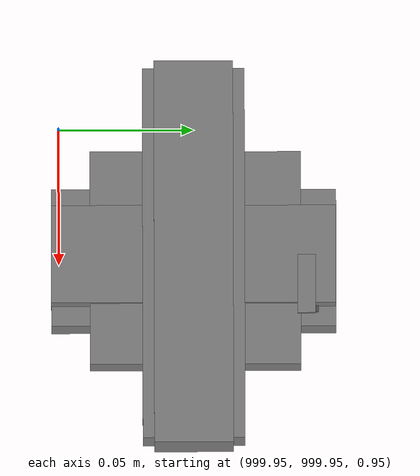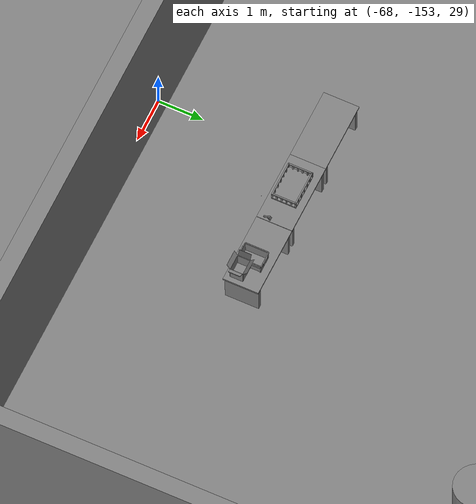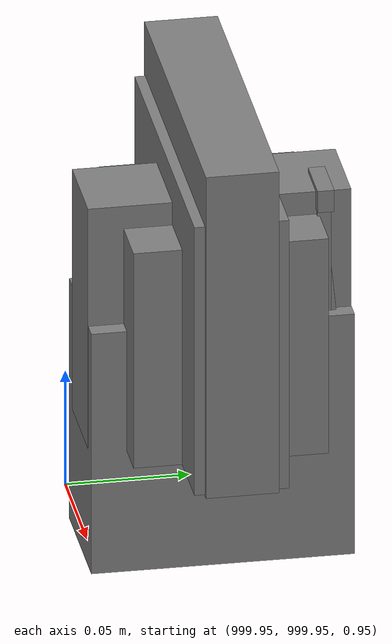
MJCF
<mujoco>
    <option gravity="0.000000000 0.000000000 -9.810000420" timestep="0.0049999999" integrator="implicitfast" density="1.225" viscosity="1.8000001e-05" noslip_iterations="10" iterations="100" sdf_iterations="50">
        <flag multiccd="disable"/>
    </option>
    <size memory="1000M"/>
    <compiler coordinate="local"/>
    <worldbody>
        <light cutoff="30" pos="0 1 1" dir="0 -1 -2"/>
        <light cutoff="30" pos="0 -1 1" dir="0 1 -2"/>
        <body pos="1000.000000000 1000.000000000 1.000000000" euler="0.000011953 0.000005123 -179.999984741" name="openloong_gripper_2f85_fix_base_usda_intel_box">
            <geom contype="1" conaffinity="1" density="1000" type="box" material="" rgba="0.500000000 0.500000000 0.500000000 1.000000000" solimp="0.899999976 0.949999988 0.001000000" friction="1.000000000 0.005000000 0.000100000" solref="0.020000000 1.000000000" margin="0" condim="3" group="0" pos="0.000000000 -0.000067139 0.000082284" quat="0.707106709 0.000000225 0.000000253 0.707106650" size="0.052800003 0.025300000 0.052800003" name="openloong_gripper_2f85_fix_base_usda_geom_82124F54_878E_4975_AB37_0D8E557AC7B4"/>
            <freejoint name="openloong_gripper_2f85_fix_base_usda_intel_box_joint"/>
            <site size="0.005000000 0.005000000 0.005000000" rgba="0.500000000 0.500000000 0.500000000 1.000000000" pos="0.000000000 0.000000000 0.000000000" quat="0.999961913 0.008726500 0.000000000 0.000000000" group="0" type="sphere" name="openloong_gripper_2f85_fix_base_usda_intel_boxsite"/>
        </body>
        <body pos="-65.912765503 -149.381179810 31.164693832" euler="11.828169823 -57.741001129 131.717422485" mocap="true" name="spotlight6_SpotLight"/>
        <body pos="1000.000000000 1000.000000000 1.000000000" euler="0.000000000 0.000000000 180.000000000" name="openloong_gripper_2f85_fix_base_usda_wifi_box">
            <geom contype="1" conaffinity="1" density="1000" type="box" material="" rgba="0.500000000 0.500000000 0.500000000 1.000000000" solimp="0.899999976 0.949999988 0.001000000" friction="1.000000000 0.005000000 0.000100000" solref="0.020000000 1.000000000" margin="0" condim="3" group="0" pos="0.000000000 0.000000000 0.058978677" quat="0.000000000 0.000000047 0.000000000 1.000000000" size="0.068499997 0.018999999 0.059000000" name="openloong_gripper_2f85_fix_base_usda_geom_D2044C23_58A0_437A_AB9E_7977BD52B5A3"/>
            <freejoint name="openloong_gripper_2f85_fix_base_usda_wifi_box_joint"/>
            <site size="0.005000000 0.005000000 0.005000000" rgba="0.500000000 0.500000000 0.500000000 1.000000000" pos="0.000000000 0.000000000 0.000000000" quat="0.999961913 0.008726500 0.000000000 0.000000000" group="0" type="sphere" name="openloong_gripper_2f85_fix_base_usda_wifi_boxsite"/>
        </body>
        <body pos="1000.000000000 999.999938965 1.000000000" euler="0.000000000 0.000000000 180.000000000" name="openloong_gripper_2f85_fix_base_usda_intelcore_i5">
            <geom contype="1" conaffinity="1" density="1000" type="box" material="" rgba="0.500000000 0.500000000 0.500000000 1.000000000" solimp="0.899999976 0.949999988 0.001000000" friction="1.000000000 0.005000000 0.000100000" solref="0.020000000 1.000000000" margin="0" condim="3" group="0" pos="0.000000000 0.000000000 0.051722717" quat="0.707106709 0.000000000 0.000000000 -0.707106769" size="0.052800000 0.018080002 0.052800000" name="openloong_gripper_2f85_fix_base_usda_geom_7EA181CF_61FD_4736_B841_724A8A15EAE9"/>
            <freejoint name="openloong_gripper_2f85_fix_base_usda_intelcore_i5_joint"/>
            <site size="0.005000000 0.005000000 0.005000000" rgba="0.500000000 0.500000000 0.500000000 1.000000000" pos="0.000000000 0.000000000 0.000000000" quat="0.999961913 0.008726534 0.000000000 0.000000000" group="0" type="sphere" name="openloong_gripper_2f85_fix_base_usda_intelcore_i5site"/>
        </body>
        <body pos="1000.000000000 1000.000000000 1.000000000" euler="0.000000000 0.000000000 180.000000000" name="openloong_gripper_2f85_fix_base_usda_cpu_fan">
            <geom contype="1" conaffinity="1" density="1000" type="box" material="" rgba="0.500000000 0.500000000 0.500000000 1.000000000" solimp="0.899999976 0.949999988 0.001000000" friction="1.000000000 0.005000000 0.000100000" solref="0.020000000 1.000000000" margin="0" condim="3" group="0" pos="0.000000000 0.000000000 0.070034981" quat="0.000000000 0.000000000 0.000000000 1.000000000" size="0.070700005 0.014699999 0.070700005" name="openloong_gripper_2f85_fix_base_usda_geom_B2216B97_6FDA_4A99_85C5_4B3ACCCDCDB0"/>
            <freejoint name="openloong_gripper_2f85_fix_base_usda_cpu_fan_joint"/>
            <site size="0.005000000 0.005000000 0.005000000" rgba="0.500000000 0.500000000 0.500000000 1.000000000" pos="0.000000000 0.000000000 0.000000000" quat="0.999961913 0.008726535 0.000000000 0.000000000" group="0" type="sphere" name="openloong_gripper_2f85_fix_base_usda_cpu_fancsite"/>
        </body>
        <body pos="-66.037864685 -149.430847168 31.165784836" euler="-103.959663391 17.095232010 16.770347595" mocap="true" name="spotlight1_SpotLight"/>
        <body pos="-66.387580872 -149.315292358 31.165575027" euler="-164.367462158 -71.621330261 -51.890804291" mocap="true" name="spotlight5_SpotLight"/>
        <body pos="1000.000000000 1000.000000000 1.000000000" euler="0.000000000 0.000000000 180.000000000" name="openloong_gripper_2f85_fix_base_usda_battery_01">
            <geom contype="1" conaffinity="1" density="1000" type="box" material="" rgba="0.500000000 0.500000000 0.500000000 1.000000000" solimp="0.899999976 0.949999988 0.001000000" friction="1.000000000 0.005000000 0.000100000" solref="0.020000000 1.000000000" margin="0" condim="3" group="0" pos="-0.011123657 -0.041940309 0.101691343" quat="1.000000000 0.000000000 0.000000000 0.000000000" size="0.010800000 0.003375000 0.004725000" name="openloong_gripper_2f85_fix_base_usda_geom_027ABAD0_84AC_4440_8CB6_E9D397E20A46"/>
            <geom contype="1" conaffinity="1" density="1000" type="box" material="" rgba="0.500000000 0.500000000 0.500000000 1.000000000" solimp="0.899999976 0.949999988 0.001000000" friction="1.000000000 0.005000000 0.000100000" solref="0.020000000 1.000000000" margin="0" condim="3" group="0" pos="-0.010876465 -0.044247437 0.047066893" quat="0.998702705 -0.050920475 0.000000000 0.000000000" size="0.009450001 0.002700000 0.024975000" name="openloong_gripper_2f85_fix_base_usda_geom_358D3EDF_5F86_4BAD_8A4E_A2DAFC9C275C"/>
            <geom contype="1" conaffinity="1" density="1000" type="box" material="" rgba="0.500000000 0.500000000 0.500000000 1.000000000" solimp="0.899999976 0.949999988 0.001000000" friction="1.000000000 0.005000000 0.000100000" solref="0.020000000 1.000000000" margin="0" condim="3" group="0" pos="-0.001235962 -0.000659180 0.047381196" quat="1.000000000 0.000000000 0.000000000 0.000000000" size="0.039420001 0.039150000 0.047250003" name="openloong_gripper_2f85_fix_base_usda_geom_1C901F08_8E8D_4B18_8358_12234D839EA7"/>
            <geom contype="1" conaffinity="1" density="1000" type="box" material="" rgba="0.500000000 0.500000000 0.500000000 1.000000000" solimp="0.899999976 0.949999988 0.001000000" friction="1.000000000 0.005000000 0.000100000" solref="0.020000000 1.000000000" margin="0" condim="3" group="0" pos="-0.010876465 -0.039138794 0.009851727" quat="1.000000000 0.000000000 0.000000000 0.000000000" size="0.009450001 0.010800000 0.013500000" name="openloong_gripper_2f85_fix_base_usda_geom_C9EB855D_3118_4879_B324_D91B6AE542AC"/>
            <geom contype="1" conaffinity="1" density="1000" type="box" material="" rgba="0.500000000 0.500000000 0.500000000 1.000000000" solimp="0.899999976 0.949999988 0.001000000" friction="1.000000000 0.005000000 0.000100000" solref="0.020000000 1.000000000" margin="0" condim="3" group="0" pos="-0.010876465 -0.041528322 0.071508206" quat="1.000000000 0.000000000 0.000000000 0.000000000" size="0.009450001 0.002700000 0.027000001" name="openloong_gripper_2f85_fix_base_usda_geom_5137C8E0_F8EC_4A6F_AE6A_93E20825F9A0"/>
            <freejoint name="openloong_gripper_2f85_fix_base_usda_battery_01_joint"/>
            <site size="0.005000000 0.005000000 0.005000000" rgba="0.500000000 0.500000000 0.500000000 1.000000000" pos="0.000000000 0.000000000 0.000000000" quat="0.999961913 0.008726500 0.000000000 0.000000000" group="0" type="sphere" name="openloong_gripper_2f85_fix_base_usda_battery_01site"/>
        </body>
        <body pos="-64.866622925 -149.383972168 30.183746338" euler="89.999984741 89.999946594 0.000000000" name="openloong_gripper_2f85_fix_base_usda_bluebox_01">
            <geom contype="1" conaffinity="1" density="1000" type="box" material="" rgba="0.500000000 0.500000000 0.500000000 1.000000000" solimp="0.899999976 0.949999988 0.001000000" friction="1.000000000 0.005000000 0.000100000" solref="0.020000000 1.000000000" margin="0" condim="3" group="0" pos="0.276580811 0.187225342 0.000068665" quat="0.707106948 0.000077471 0.707106352 0.000077486" size="0.100000001 0.057999998 0.010000000" name="openloong_gripper_2f85_fix_base_usda_geom_08C5BADF_8E42_454C_BE21_395E492882C0"/>
            <geom contype="1" conaffinity="1" density="1000" type="box" material="" rgba="0.500000000 0.500000000 0.500000000 1.000000000" solimp="0.899999976 0.949999988 0.001000000" friction="1.000000000 0.005000000 0.000100000" solref="0.020000000 1.000000000" margin="0" condim="3" group="0" pos="0.000000000 0.002883911 0.000000000" quat="0.999999881 0.000000000 0.000000000 0.000000000" size="0.254000008 0.003000000 0.172000006" name="openloong_gripper_2f85_fix_base_usda_geom_DC9ECC38_DEEC_4102_A747_FB9A10CC9C99"/>
            <geom contype="1" conaffinity="1" density="1000" type="box" material="" rgba="0.500000000 0.500000000 0.500000000 1.000000000" solimp="0.899999976 0.949999988 0.001000000" friction="1.000000000 0.005000000 0.000100000" solref="0.020000000 1.000000000" margin="0" condim="3" group="0" pos="0.000000000 0.124874115 0.173484802" quat="0.999796331 0.020176515 -0.000000015 0.000000030" size="0.259999990 0.119999997 0.007000000" name="openloong_gripper_2f85_fix_base_usda_geom_9756DA69_5995_43F7_821C_9853A2FD6364"/>
            <geom contype="1" conaffinity="1" density="1000" type="box" material="" rgba="0.500000000 0.500000000 0.500000000 1.000000000" solimp="0.899999976 0.949999988 0.001000000" friction="1.000000000 0.005000000 0.000100000" solref="0.020000000 1.000000000" margin="0" condim="3" group="0" pos="0.000000000 0.124874115 -0.173469543" quat="0.999796331 -0.020176545 -0.000000015 0.000000000" size="0.259999990 0.119999997 0.007000000" name="openloong_gripper_2f85_fix_base_usda_geom_C2E0450E_374B_4D34_B8B6_A7A60A63BB35"/>
            <geom contype="1" conaffinity="1" density="1000" type="box" material="" rgba="0.500000000 0.500000000 0.500000000 1.000000000" solimp="0.899999976 0.949999988 0.001000000" friction="1.000000000 0.005000000 0.000100000" solref="0.020000000 1.000000000" margin="0" condim="3" group="0" pos="0.000000000 0.214008331 0.188980103" quat="0.999912977 0.013176724 0.000000015 0.000000000" size="0.259999990 0.029999999 0.012500000" name="openloong_gripper_2f85_fix_base_usda_geom_0DFC292C_B10A_48AC_B715_6BEE791C904B"/>
            <geom contype="1" conaffinity="1" density="1000" type="box" material="" rgba="0.500000000 0.500000000 0.500000000 1.000000000" solimp="0.899999976 0.949999988 0.001000000" friction="1.000000000 0.005000000 0.000100000" solref="0.020000000 1.000000000" margin="0" condim="3" group="0" pos="-0.258361816 0.125289917 0.001876831" quat="0.702796936 -0.020792112 0.710783124 0.020769298" size="0.189999998 0.119999997 0.009000000" name="openloong_gripper_2f85_fix_base_usda_geom_F587F4ED_7C73_4245_B117_83BCAD7A6D9E"/>
            <geom contype="1" conaffinity="1" density="1000" type="box" material="" rgba="0.500000000 0.500000000 0.500000000 1.000000000" solimp="0.899999976 0.949999988 0.001000000" friction="1.000000000 0.005000000 0.000100000" solref="0.020000000 1.000000000" margin="0" condim="3" group="0" pos="0.000000000 0.214008331 -0.188980103" quat="0.999912977 -0.013176769 0.000000030 0.000000015" size="0.259999990 0.029999999 0.012500000" name="openloong_gripper_2f85_fix_base_usda_geom_386C33B9_F7FF_4052_9B63_91B9C519446E"/>
            <geom contype="1" conaffinity="1" density="1000" type="box" material="" rgba="0.500000000 0.500000000 0.500000000 1.000000000" solimp="0.899999976 0.949999988 0.001000000" friction="1.000000000 0.005000000 0.000100000" solref="0.020000000 1.000000000" margin="0" condim="3" group="0" pos="-0.276611328 0.187225342 0.000068665" quat="0.707106650 0.000077441 0.707106709 0.000077456" size="0.100000001 0.057999998 0.010000000" name="openloong_gripper_2f85_fix_base_usda_geom_1C3D4230_2FD3_47F4_B1C9_81FFD2454D5C"/>
            <geom contype="1" conaffinity="1" density="1000" type="box" material="" rgba="0.500000000 0.500000000 0.500000000 1.000000000" solimp="0.899999976 0.949999988 0.001000000" friction="1.000000000 0.005000000 0.000100000" solref="0.020000000 1.000000000" margin="0" condim="3" group="0" pos="0.258331299 0.125289917 0.001876831" quat="0.702851415 0.018856421 0.710823774 -0.019329369" size="0.189999998 0.119999997 0.009000000" name="openloong_gripper_2f85_fix_base_usda_geom_57985849_1290_401D_932B_59BB4A37BE69"/>
            <freejoint name="openloong_gripper_2f85_fix_base_usda_bluebox_01_joint"/>
            <site size="0.005000000 0.005000000 0.005000000" rgba="0.500000000 0.500000000 0.500000000 1.000000000" pos="0.000000000 0.000000000 0.000000000" quat="0.999961913 0.008726534 0.000000000 0.000000000" group="0" type="sphere" name="openloong_gripper_2f85_fix_base_usda_bluebox_01site"/>
        </body>
        <body pos="-64.496299744 -149.491867065 30.235729218" euler="0.000000000 0.000000000 89.999946594" name="openloong_gripper_2f85_fix_base_usda_cardboardbox_01">
            <geom contype="1" conaffinity="1" density="1000" type="box" material="" rgba="0.500000000 0.500000000 0.500000000 1.000000000" solimp="0.899999976 0.949999988 0.001000000" friction="1.000000000 0.005000000 0.000100000" solref="0.020000000 1.000000000" margin="0" condim="3" group="0" pos="-0.003166199 -0.004086494 0.005052090" quat="1.000000000 0.000000000 0.000000000 0.000000000" size="0.142499998 0.177500010 0.005000000" name="openloong_gripper_2f85_fix_base_usda_geom_D428446D_2DFC_4516_AEBF_8F41033F452A"/>
            <geom contype="1" conaffinity="1" density="1000" type="box" material="" rgba="0.500000000 0.500000000 0.500000000 1.000000000" solimp="0.899999976 0.949999988 0.001000000" friction="1.000000000 0.005000000 0.000100000" solref="0.020000000 1.000000000" margin="0" condim="3" group="0" pos="-0.003166199 0.170316696 0.150570869" quat="1.000000000 0.000000000 0.000000000 0.000000000" size="0.142499998 0.005000000 0.149999991" name="openloong_gripper_2f85_fix_base_usda_geom_58468E6E_47B4_4BE7_BC3A_8470E0B15F65"/>
            <geom contype="1" conaffinity="1" density="1000" type="box" material="" rgba="0.500000000 0.500000000 0.500000000 1.000000000" solimp="0.899999976 0.949999988 0.001000000" friction="1.000000000 0.005000000 0.000100000" solref="0.020000000 1.000000000" margin="0" condim="3" group="0" pos="-0.147399902 -0.005307198 0.150570869" quat="1.000000000 0.000000000 0.000000000 0.000000000" size="0.005000000 0.177500010 0.149999991" name="openloong_gripper_2f85_fix_base_usda_geom_2A7CAAE3_1A09_4865_8F79_94608CDD9152"/>
            <geom contype="1" conaffinity="1" density="1000" type="box" material="" rgba="0.500000000 0.500000000 0.500000000 1.000000000" solimp="0.899999976 0.949999988 0.001000000" friction="1.000000000 0.005000000 0.000100000" solref="0.020000000 1.000000000" margin="0" condim="3" group="0" pos="0.140275955 -0.005307198 0.150570869" quat="1.000000000 0.000000000 0.000000000 0.000000000" size="0.005000000 0.177500010 0.149999991" name="openloong_gripper_2f85_fix_base_usda_geom_0A9695CA_2C6C_47A5_A2BD_B3C3075A5572"/>
            <geom contype="1" conaffinity="1" density="1000" type="box" material="" rgba="0.500000000 0.500000000 0.500000000 1.000000000" solimp="0.899999976 0.949999988 0.001000000" friction="1.000000000 0.005000000 0.000100000" solref="0.020000000 1.000000000" margin="0" condim="3" group="0" pos="-0.003166199 -0.181550980 0.150570869" quat="1.000000000 0.000000000 0.000000000 0.000000000" size="0.142499998 0.005000000 0.149999991" name="openloong_gripper_2f85_fix_base_usda_geom_675AB7F2_317E_4E3B_A8A0_350BB5686028"/>
            <freejoint name="openloong_gripper_2f85_fix_base_usda_cardboardbox_01_joint"/>
            <site size="0.005000000 0.005000000 0.005000000" rgba="0.500000000 0.500000000 0.500000000 1.000000000" pos="0.000000000 0.000000000 0.000000000" quat="0.999961913 0.008726535 0.000000000 0.000000000" group="0" type="sphere" name="openloong_gripper_2f85_fix_base_usda_site_68D0B4E1_F650_4B19_86DD_6A3D2ED7B1DC"/>
            <body pos="0.139160156 -0.004048347 0.301930904" euler="-179.999954224 49.383502960 179.999954224" name="openloong_gripper_2f85_fix_base_usda_A1_006">
                <geom contype="1" conaffinity="1" density="1000" type="box" material="" rgba="0.500000000 0.500000000 0.500000000 1.000000000" solimp="0.899999976 0.949999988 0.001000000" friction="1.000000000 0.005000000 0.000100000" solref="0.020000000 1.000000000" margin="0" condim="3" group="0" pos="-0.071587563 0.000009537 0.001745224" quat="0.999999881 0.000000000 0.000000000 0.000000000" size="0.071249999 0.179999992 0.002500000" name="openloong_gripper_2f85_fix_base_usda_geom_F546BF8E_B738_4BF3_81F5_757985239019"/>
                <joint armature="0" stiffness="0.07" damping="0.0099999998" axis="0.000000 1.000000 0.000000" type="hinge" name="openloong_gripper_2f85_fix_base_usda_A1_006"/>
            </body>
            <body pos="-0.145902634 -0.004086494 0.301938057" euler="-180.000000000 -60.000011444 -180.000000000" name="openloong_gripper_2f85_fix_base_usda_A2_006">
                <geom contype="1" conaffinity="1" density="1000" type="box" material="" rgba="0.500000000 0.500000000 0.500000000 1.000000000" solimp="0.899999976 0.949999988 0.001000000" friction="1.000000000 0.005000000 0.000100000" solref="0.020000000 1.000000000" margin="0" condim="3" group="0" pos="0.071268082 0.000009537 0.002717972" quat="0.000002921 0.000000000 -0.000000030 0.999999881" size="0.071249999 0.179999992 0.002500000" name="openloong_gripper_2f85_fix_base_usda_geom_823FD431_8B96_4B0C_808A_4BF15B0DE733"/>
                <joint armature="0" stiffness="0.07" damping="0.0099999998" axis="0.000000 1.000000 0.000000" type="hinge" name="openloong_gripper_2f85_fix_base_usda_A2_006"/>
            </body>
            <body pos="-0.003385544 0.175991058 0.301930904" euler="-125.858116150 -0.000004561 0.000002331" name="openloong_gripper_2f85_fix_base_usda_B2_006">
                <geom contype="1" conaffinity="1" density="1000" type="box" material="" rgba="0.500000000 0.500000000 0.500000000 1.000000000" solimp="0.899999976 0.949999988 0.001000000" friction="1.000000000 0.005000000 0.000100000" solref="0.020000000 1.000000000" margin="0" condim="3" group="0" pos="0.000009537 -0.070939064 -0.002470016" quat="0.999614120 0.027776197 -0.000000015 0.000000030" size="0.137500003 0.064999998 0.005000000" name="openloong_gripper_2f85_fix_base_usda_geom_6A6D8D12_FFE7_4A47_94CD_B0794BB02731"/>
                <joint armature="0" stiffness="0.07" damping="0.0099999998" axis="1.000000 0.000000 0.000000" type="hinge" name="openloong_gripper_2f85_fix_base_usda_B2_006"/>
            </body>
            <body pos="-0.003385544 -0.184140205 0.301938057" euler="147.805557251 0.000000000 0.000000000" name="openloong_gripper_2f85_fix_base_usda_B1_006">
                <geom contype="1" conaffinity="1" density="1000" type="box" material="" rgba="0.500000000 0.500000000 0.500000000 1.000000000" solimp="0.899999976 0.949999988 0.001000000" friction="1.000000000 0.005000000 0.000100000" solref="0.020000000 1.000000000" margin="0" condim="3" group="0" pos="-0.000028610 0.070202351 -0.002703667" quat="0.999614179 -0.027776167 0.000000000 0.000000000" size="0.137500003 0.064999998 0.005000000" name="openloong_gripper_2f85_fix_base_usda_geom_A916AF6E_5071_4893_B69D_12C85A7D6EB7"/>
                <joint armature="0" stiffness="0.07" damping="0.0099999998" axis="1.000000 0.000000 0.000000" type="hinge" name="openloong_gripper_2f85_fix_base_usda_B1_006"/>
            </body>
        </body>
        <body pos="-65.882858276 -149.481979370 30.229999542" euler="-64.487716675 0.000000000 0.000000000" name="openloong_gripper_2f85_fix_base_usda_Barcode">
            <geom contype="1" conaffinity="1" density="1000" type="box" material="" rgba="0.500000000 0.500000000 0.500000000 1.000000000" solimp="0.899999976 0.949999988 0.001000000" friction="1.000000000 0.005000000 0.000100000" solref="0.020000000 1.000000000" margin="0" condim="3" group="0" pos="0.000000000 0.013038635 0.001419067" quat="0.000000000 0.000000000 0.000000000 1.000000119" size="0.034000002 0.010000000 0.017999999" name="openloong_gripper_2f85_fix_base_usda_geom_6C62C234_1E0B_4C93_838E_7820EE63C087"/>
            <geom contype="1" conaffinity="1" density="1000" type="box" material="" rgba="0.500000000 0.500000000 0.500000000 1.000000000" solimp="0.899999976 0.949999988 0.001000000" friction="1.000000000 0.005000000 0.000100000" solref="0.020000000 1.000000000" margin="0" condim="3" group="0" pos="0.000000000 -0.035301208 -0.007095337" quat="0.000000000 0.000000000 -0.043619365 0.999048233" size="0.028999999 0.010000000 0.020000000" name="openloong_gripper_2f85_fix_base_usda_geom_854B13B6_93B3_4207_8181_71C2D0B0899B"/>
            <geom contype="1" conaffinity="1" density="1000" type="box" material="" rgba="0.500000000 0.500000000 0.500000000 1.000000000" solimp="0.899999976 0.949999988 0.001000000" friction="1.000000000 0.005000000 0.000100000" solref="0.020000000 1.000000000" margin="0" condim="3" group="0" pos="0.000000000 -0.043411255 -0.011749268" quat="0.922262907 0.386563420 0.000000000 0.000000000" size="0.026000001 0.010000000 0.020000000" name="openloong_gripper_2f85_fix_base_usda_geom_7854B701_4866_4957_9A4A_B066F4F9B551"/>
            <geom contype="1" conaffinity="1" density="1000" type="box" material="" rgba="0.500000000 0.500000000 0.500000000 1.000000000" solimp="0.899999976 0.949999988 0.001000000" friction="1.000000000 0.005000000 0.000100000" solref="0.020000000 1.000000000" margin="0" condim="3" group="0" pos="0.000000000 -0.016967773 -0.031860352" quat="0.000000000 0.000000000 0.000000000 1.000000119" size="0.008000000 0.010000000 0.013000000" name="openloong_gripper_2f85_fix_base_usda_geom_8ED367B2_51B9_472E_BBBC_3C5DB6D8455D"/>
            <geom contype="1" conaffinity="1" density="1000" type="box" material="" rgba="0.500000000 0.500000000 0.500000000 1.000000000" solimp="0.899999976 0.949999988 0.001000000" friction="1.000000000 0.005000000 0.000100000" solref="0.020000000 1.000000000" margin="0" condim="3" group="0" pos="0.000000000 -0.001869202 0.000312805" quat="0.953716993 0.300705761 0.000000000 0.000000000" size="0.032000002 0.010000000 0.018999999" name="openloong_gripper_2f85_fix_base_usda_geom_0DD01E6C_8A80_4831_92C2_8FD7CF3A5C34"/>
            <geom contype="1" conaffinity="1" density="1000" type="box" material="" rgba="0.500000000 0.500000000 0.500000000 1.000000000" solimp="0.899999976 0.949999988 0.001000000" friction="1.000000000 0.005000000 0.000100000" solref="0.020000000 1.000000000" margin="0" condim="3" group="0" pos="0.000000000 -0.019531250 -0.003173828" quat="0.953716993 0.300705761 0.000000000 0.000000000" size="0.030999999 0.010000000 0.020000000" name="openloong_gripper_2f85_fix_base_usda_geom_1DC6CD6F_A526_4BFB_BC33_48136C5D5B95"/>
            <geom contype="1" conaffinity="1" density="1000" type="box" material="" rgba="0.500000000 0.500000000 0.500000000 1.000000000" solimp="0.899999976 0.949999988 0.001000000" friction="1.000000000 0.005000000 0.000100000" solref="0.020000000 1.000000000" margin="0" condim="3" group="0" pos="0.000000000 -0.035301208 -0.007095337" quat="0.953716993 0.300705761 0.000000000 0.000000000" size="0.028999999 0.010000000 0.020000000" name="openloong_gripper_2f85_fix_base_usda_geom_2EF80CE4_8E72_40D9_B656_59CEC8FFC3A1"/>
            <geom contype="1" conaffinity="1" density="1000" type="box" material="" rgba="0.500000000 0.500000000 0.500000000 1.000000000" solimp="0.899999976 0.949999988 0.001000000" friction="1.000000000 0.005000000 0.000100000" solref="0.020000000 1.000000000" margin="0" condim="3" group="0" pos="0.000000000 -0.042617798 -0.071121216" quat="0.000000000 0.000000000 0.000000000 1.000000119" size="0.013000000 0.021000000 0.059999999" name="openloong_gripper_2f85_fix_base_usda_geom_755BACC4_D5EA_4188_84E9_09C3B0300CB3"/>
            <freejoint name="openloong_gripper_2f85_fix_base_usda_Barcode_joint"/>
            <site size="0.005000000 0.005000000 0.005000000" rgba="0.500000000 0.500000000 0.500000000 1.000000000" pos="0.000000000 0.000000000 0.000000000" quat="1.000000000 0.000000000 0.000000000 0.000000000" group="0" type="sphere" name="openloong_gripper_2f85_fix_base_usda_Barcode_site"/>
        </body>
        <body pos="-66.745018005 -149.392349243 30.184000015" euler="0.000000000 0.000000000 89.999946594" name="[22329773944033]_Basket_01">
            <geom contype="1" conaffinity="1" density="1000" type="box" material="" rgba="0.500000000 0.500000000 0.500000000 1.000000000" solimp="0.899999976 0.949999988 0.001000000" friction="1.000000000 0.005000000 0.000100000" solref="0.020000000 1.000000000" margin="0" condim="3" group="0" pos="-0.052425385 0.389207840 0.089787483" quat="0.707107008 0.000000000 0.000000000 0.707106411" size="0.014249999 0.014249999 0.059999999" name="[22329773944033]_geom_06F007D1_7D7F_4242_9BC3_6C922F62EBA4"/>
            <geom contype="1" conaffinity="1" density="1000" type="box" material="" rgba="0.500000000 0.500000000 0.500000000 1.000000000" solimp="0.899999976 0.949999988 0.001000000" friction="1.000000000 0.005000000 0.000100000" solref="0.020000000 1.000000000" margin="0" condim="3" group="0" pos="0.264015198 -0.133043289 0.089787483" quat="0.707107008 0.000000000 0.000000000 0.707106411" size="0.014249999 0.014249999 0.059999999" name="[22329773944033]_geom_13AD205F_C117_4B7A_973D_F706FEA90B46"/>
            <geom contype="1" conaffinity="1" density="1000" type="box" material="" rgba="0.500000000 0.500000000 0.500000000 1.000000000" solimp="0.899999976 0.949999988 0.001000000" friction="1.000000000 0.005000000 0.000100000" solref="0.020000000 1.000000000" margin="0" condim="3" group="0" pos="-0.264015198 -0.265548706 0.089793205" quat="0.707107008 0.000000000 0.000000000 0.707106411" size="0.014249999 0.014249999 0.059999999" name="[22329773944033]_geom_BD2CF853_4847_487C_A19F_69E644EC7991"/>
            <geom contype="1" conaffinity="1" density="1000" type="box" material="" rgba="0.500000000 0.500000000 0.500000000 1.000000000" solimp="0.899999976 0.949999988 0.001000000" friction="1.000000000 0.005000000 0.000100000" solref="0.020000000 1.000000000" margin="0" condim="3" group="0" pos="-0.160263062 -0.389322281 0.089793205" quat="0.707107008 0.000000000 0.000000000 0.707106411" size="0.014249999 0.014249999 0.059999999" name="[22329773944033]_geom_7245F31F_59BB_4EA8_B76E_1A5795AF2FAF"/>
            <geom contype="1" conaffinity="1" density="1000" type="box" material="" rgba="0.500000000 0.500000000 0.500000000 1.000000000" solimp="0.899999976 0.949999988 0.001000000" friction="1.000000000 0.005000000 0.000100000" solref="0.020000000 1.000000000" margin="0" condim="3" group="0" pos="0.162265778 -0.389322281 0.089787483" quat="0.707107008 0.000000000 0.000000000 0.707106411" size="0.014249999 0.014249999 0.059999999" name="[22329773944033]_geom_45136F24_AAC2_4650_8F3B_A0273E356905"/>
            <geom contype="1" conaffinity="1" density="1000" type="box" material="" rgba="0.500000000 0.500000000 0.500000000 1.000000000" solimp="0.899999976 0.949999988 0.001000000" friction="1.000000000 0.005000000 0.000100000" solref="0.020000000 1.000000000" margin="0" condim="3" group="0" pos="0.264015198 0.389207840 0.089787483" quat="0.707107008 0.000000000 0.000000000 0.707106411" size="0.014249999 0.014249999 0.059999999" name="[22329773944033]_geom_517FB562_548E_4797_9B48_CBFA6E899B4A"/>
            <geom contype="1" conaffinity="1" density="1000" type="box" material="" rgba="0.500000000 0.500000000 0.500000000 1.000000000" solimp="0.899999976 0.949999988 0.001000000" friction="1.000000000 0.005000000 0.000100000" solref="0.020000000 1.000000000" margin="0" condim="3" group="0" pos="-0.264015198 -0.133043289 0.089793205" quat="0.707107008 0.000000000 0.000000000 0.707106411" size="0.014249999 0.014249999 0.059999999" name="[22329773944033]_geom_6F621EEA_E41A_49AF_B488_662E66A78437"/>
            <geom contype="1" conaffinity="1" density="1000" type="box" material="" rgba="0.500000000 0.500000000 0.500000000 1.000000000" solimp="0.899999976 0.949999988 0.001000000" friction="1.000000000 0.005000000 0.000100000" solref="0.020000000 1.000000000" margin="0" condim="3" group="0" pos="-0.264026642 0.269256592 0.089793205" quat="0.707107008 0.000000000 0.000000000 0.707106411" size="0.014249999 0.014249999 0.059999999" name="[22329773944033]_geom_78BF7996_14D2_4CBB_ABB9_F958AFF7279F"/>
            <geom contype="1" conaffinity="1" density="1000" type="box" material="" rgba="0.500000000 0.500000000 0.500000000 1.000000000" solimp="0.899999976 0.949999988 0.001000000" friction="1.000000000 0.005000000 0.000100000" solref="0.020000000 1.000000000" margin="0" condim="3" group="0" pos="0.054462433 0.389207840 0.089787483" quat="0.707107008 0.000000000 0.000000000 0.707106411" size="0.014249999 0.014249999 0.059999999" name="[22329773944033]_geom_941DBD78_D720_44E5_BDB6_D996FB716772"/>
            <geom contype="1" conaffinity="1" density="1000" type="box" material="" rgba="0.500000000 0.500000000 0.500000000 1.000000000" solimp="0.899999976 0.949999988 0.001000000" friction="1.000000000 0.005000000 0.000100000" solref="0.020000000 1.000000000" margin="0" condim="3" group="0" pos="0.054462433 -0.389322281 0.089787483" quat="0.707107008 0.000000000 0.000000000 0.707106411" size="0.014249999 0.014249999 0.059999999" name="[22329773944033]_geom_45907331_ED8B_4102_9002_C76666AEDD06"/>
            <geom contype="1" conaffinity="1" density="1000" type="box" material="" rgba="0.500000000 0.500000000 0.500000000 1.000000000" solimp="0.899999976 0.949999988 0.001000000" friction="1.000000000 0.005000000 0.000100000" solref="0.020000000 1.000000000" margin="0" condim="3" group="0" pos="0.264015198 0.269256592 0.089793205" quat="0.707107008 0.000000000 0.000000000 0.707106411" size="0.014249999 0.014249999 0.059999999" name="[22329773944033]_geom_543616E0_3F8E_4D8C_A337_700D62313A4A"/>
            <geom contype="1" conaffinity="1" density="1000" type="box" material="" rgba="0.500000000 0.500000000 0.500000000 1.000000000" solimp="0.899999976 0.949999988 0.001000000" friction="1.000000000 0.005000000 0.000100000" solref="0.020000000 1.000000000" margin="0" condim="3" group="0" pos="0.264015198 -0.389322281 0.089787483" quat="0.707107008 0.000000000 0.000000000 0.707106411" size="0.014249999 0.014249999 0.059999999" name="[22329773944033]_geom_03CE3F64_DC2C_466D_A2D5_76903DF2351B"/>
            <geom contype="1" conaffinity="1" density="1000" type="box" material="" rgba="0.500000000 0.500000000 0.500000000 1.000000000" solimp="0.899999976 0.949999988 0.001000000" friction="1.000000000 0.005000000 0.000100000" solref="0.020000000 1.000000000" margin="0" condim="3" group="0" pos="0.000000000 0.000000000 0.015998840" quat="0.707107008 0.000000000 0.000000000 0.707106411" size="0.403499991 0.279000014 0.015750000" name="[22329773944033]_geom_CB20C206_F70A_4092_949D_A87F7D25E706"/>
            <geom contype="1" conaffinity="1" density="1000" type="box" material="" rgba="0.500000000 0.500000000 0.500000000 1.000000000" solimp="0.899999976 0.949999988 0.001000000" friction="1.000000000 0.005000000 0.000100000" solref="0.020000000 1.000000000" margin="0" condim="3" group="0" pos="0.000000000 -0.389476776 0.163619041" quat="0.707107008 0.000000000 0.000000000 0.707106411" size="0.015000000 0.277500004 0.015750000" name="[22329773944033]_geom_24E0561F_D74B_4E83_A04C_D194A3998DBE"/>
            <geom contype="1" conaffinity="1" density="1000" type="box" material="" rgba="0.500000000 0.500000000 0.500000000 1.000000000" solimp="0.899999976 0.949999988 0.001000000" friction="1.000000000 0.005000000 0.000100000" solref="0.020000000 1.000000000" margin="0" condim="3" group="0" pos="0.162265778 0.389207840 0.089787483" quat="0.707107008 0.000000000 0.000000000 0.707106411" size="0.014249999 0.014249999 0.059999999" name="[22329773944033]_geom_7EACD630_C5C2_4F55_B83D_2F28DEEFC38B"/>
            <geom contype="1" conaffinity="1" density="1000" type="box" material="" rgba="0.500000000 0.500000000 0.500000000 1.000000000" solimp="0.899999976 0.949999988 0.001000000" friction="1.000000000 0.005000000 0.000100000" solref="0.020000000 1.000000000" margin="0" condim="3" group="0" pos="0.000000000 0.389471054 0.163619041" quat="0.707107008 0.000000000 0.000000000 0.707106411" size="0.015000000 0.277500004 0.015750000" name="[22329773944033]_geom_5C90FB29_075B_4630_837B_046CAE5A4E46"/>
            <geom contype="1" conaffinity="1" density="1000" type="box" material="" rgba="0.500000000 0.500000000 0.500000000 1.000000000" solimp="0.899999976 0.949999988 0.001000000" friction="1.000000000 0.005000000 0.000100000" solref="0.020000000 1.000000000" margin="0" condim="3" group="0" pos="-0.263511658 0.000000000 0.163619041" quat="0.707107008 0.000000000 0.000000000 0.707106411" size="0.403499991 0.015000000 0.015750000" name="[22329773944033]_geom_3212DA57_85C8_4259_B589_E0ACF5024B56"/>
            <geom contype="1" conaffinity="1" density="1000" type="box" material="" rgba="0.500000000 0.500000000 0.500000000 1.000000000" solimp="0.899999976 0.949999988 0.001000000" friction="1.000000000 0.005000000 0.000100000" solref="0.020000000 1.000000000" margin="0" condim="3" group="0" pos="-0.264015198 0.141334534 0.089793205" quat="0.707107008 0.000000000 0.000000000 0.707106411" size="0.014249999 0.014249999 0.059999999" name="[22329773944033]_geom_37016E26_543A_496E_8227_0058F593C377"/>
            <geom contype="1" conaffinity="1" density="1000" type="box" material="" rgba="0.500000000 0.500000000 0.500000000 1.000000000" solimp="0.899999976 0.949999988 0.001000000" friction="1.000000000 0.005000000 0.000100000" solref="0.020000000 1.000000000" margin="0" condim="3" group="0" pos="0.264015198 -0.265548706 0.089787483" quat="0.707107008 0.000000000 0.000000000 0.707106411" size="0.014249999 0.014249999 0.059999999" name="[22329773944033]_geom_DCCC6B93_B8CE_417D_B5C1_4E10C4809FDD"/>
            <geom contype="1" conaffinity="1" density="1000" type="box" material="" rgba="0.500000000 0.500000000 0.500000000 1.000000000" solimp="0.899999976 0.949999988 0.001000000" friction="1.000000000 0.005000000 0.000100000" solref="0.020000000 1.000000000" margin="0" condim="3" group="0" pos="-0.160263062 0.389207840 0.089787483" quat="0.707107008 0.000000000 0.000000000 0.707106411" size="0.014249999 0.014249999 0.059999999" name="[22329773944033]_geom_58EB364F_20E7_4673_90E6_17CB40293EF7"/>
            <geom contype="1" conaffinity="1" density="1000" type="box" material="" rgba="0.500000000 0.500000000 0.500000000 1.000000000" solimp="0.899999976 0.949999988 0.001000000" friction="1.000000000 0.005000000 0.000100000" solref="0.020000000 1.000000000" margin="0" condim="3" group="0" pos="-0.052425385 -0.389322281 0.089787483" quat="0.707107008 0.000000000 0.000000000 0.707106411" size="0.014249999 0.014249999 0.059999999" name="[22329773944033]_geom_9849A30A_E59D_4C50_A2A3_DE9DE5CD267D"/>
            <geom contype="1" conaffinity="1" density="1000" type="box" material="" rgba="0.500000000 0.500000000 0.500000000 1.000000000" solimp="0.899999976 0.949999988 0.001000000" friction="1.000000000 0.005000000 0.000100000" solref="0.020000000 1.000000000" margin="0" condim="3" group="0" pos="-0.264026642 -0.389322281 0.089793205" quat="0.707107008 0.000000000 0.000000000 0.707106411" size="0.014249999 0.014249999 0.059999999" name="[22329773944033]_geom_7CA86351_49CC_455E_8134_3E0B7B4056EC"/>
            <geom contype="1" conaffinity="1" density="1000" type="box" material="" rgba="0.500000000 0.500000000 0.500000000 1.000000000" solimp="0.899999976 0.949999988 0.001000000" friction="1.000000000 0.005000000 0.000100000" solref="0.020000000 1.000000000" margin="0" condim="3" group="0" pos="0.264015198 0.141334534 0.089787483" quat="0.707107008 0.000000000 0.000000000 0.707106411" size="0.014249999 0.014249999 0.059999999" name="[22329773944033]_geom_1AA48866_0B29_46E7_8757_CCE882F2CB67"/>
            <geom contype="1" conaffinity="1" density="1000" type="box" material="" rgba="0.500000000 0.500000000 0.500000000 1.000000000" solimp="0.899999976 0.949999988 0.001000000" friction="1.000000000 0.005000000 0.000100000" solref="0.020000000 1.000000000" margin="0" condim="3" group="0" pos="-0.264015198 0.389207840 0.089793205" quat="0.707107008 0.000000000 0.000000000 0.707106411" size="0.014249999 0.014249999 0.059999999" name="[22329773944033]_geom_24198B78_6CBE_4D41_A14E_E472424B1F6B"/>
            <geom contype="1" conaffinity="1" density="1000" type="box" material="" rgba="0.500000000 0.500000000 0.500000000 1.000000000" solimp="0.899999976 0.949999988 0.001000000" friction="1.000000000 0.005000000 0.000100000" solref="0.020000000 1.000000000" margin="0" condim="3" group="0" pos="0.264015198 0.004480362 0.089787483" quat="0.707107008 0.000000000 0.000000000 0.707106411" size="0.014249999 0.014249999 0.059999999" name="[22329773944033]_geom_937143B4_52FD_47BE_BAEB_21A2EEBCD3B8"/>
            <geom contype="1" conaffinity="1" density="1000" type="box" material="" rgba="0.500000000 0.500000000 0.500000000 1.000000000" solimp="0.899999976 0.949999988 0.001000000" friction="1.000000000 0.005000000 0.000100000" solref="0.020000000 1.000000000" margin="0" condim="3" group="0" pos="0.263694763 -0.000011444 0.163619041" quat="0.707107008 0.000000000 0.000000000 0.707106411" size="0.403499991 0.015000000 0.015750000" name="[22329773944033]_geom_CDC17DCF_22D3_4F7D_B87C_9A7A564BB58C"/>
            <geom contype="1" conaffinity="1" density="1000" type="box" material="" rgba="0.500000000 0.500000000 0.500000000 1.000000000" solimp="0.899999976 0.949999988 0.001000000" friction="1.000000000 0.005000000 0.000100000" solref="0.020000000 1.000000000" margin="0" condim="3" group="0" pos="-0.264015198 0.004480362 0.089793205" quat="0.707107008 0.000000000 0.000000000 0.707106411" size="0.014249999 0.014249999 0.059999999" name="[22329773944033]_geom_7AF36062_B5DB_43BC_963B_238C4181F729"/>
            <freejoint name="[22329773944033]_joint_B5F120B4_AE23_47FB_9CDD_9AF7672C1397"/>
        </body>
        <body pos="0.000000000 0.000000000 0.000000000" euler="0.000000000 0.000000000 0.000000000" name="Static Objects_Static Objects">
            <geom contype="1" conaffinity="1" density="1000" type="box" material="" rgba="0.500000000 0.500000000 0.500000000 1.000000000" solimp="0.899999976 0.949999988 0.001000000" friction="1.000000000 0.005000000 0.000100000" solref="0.020000000 1.000000000" margin="0" condim="3" group="0" pos="-67.544113159 -149.365814209 29.727830887" quat="0.500000417 0.499999970 0.499999553 0.499999970" size="0.381000012 0.319999993 0.041000001" name="Static Objects_geom_C53AD0BF_2B76_4DAC_AE88_7494A7F33C6B"/>
            <geom contype="1" conaffinity="1" density="1000" type="box" material="" rgba="0.500000000 0.500000000 0.500000000 1.000000000" solimp="0.899999976 0.949999988 0.001000000" friction="1.000000000 0.005000000 0.000100000" solref="0.020000000 1.000000000" margin="0" condim="3" group="0" pos="-68.239501953 -149.365814209 30.086868286" quat="0.500000417 0.499999970 0.499999553 0.499999970" size="0.370999992 0.039500002 0.745000005" name="Static Objects_geom_F967E6D2_E3F4_4574_8F09_B0172BD75D4D"/>
            <geom contype="1" conaffinity="1" density="1000" type="box" material="" rgba="0.500000000 0.500000000 0.500000000 1.000000000" solimp="0.899999976 0.949999988 0.001000000" friction="1.000000000 0.005000000 0.000100000" solref="0.020000000 1.000000000" margin="0" condim="3" group="0" pos="-68.239501953 -149.365814209 30.147235870" quat="0.500000417 0.499999970 0.499999553 0.499999970" size="0.400000006 0.022000000 0.800000012" name="Static Objects_geom_0732DCC8_4E66_402E_AF9A_12B798C7B308"/>
            <geom contype="1" conaffinity="1" density="1000" type="box" material="" rgba="0.500000000 0.500000000 0.500000000 1.000000000" solimp="0.899999976 0.949999988 0.001000000" friction="1.000000000 0.005000000 0.000100000" solref="0.020000000 1.000000000" margin="0" condim="3" group="0" pos="-68.934890747 -149.365814209 29.727830887" quat="0.500000417 0.499999970 0.499999553 0.499999970" size="0.381000012 0.319999993 0.041000001" name="Static Objects_geom_8203572D_A17C_4B7F_A3A3_AE38F9F8AE0F"/>
            <geom contype="1" conaffinity="1" density="1000" type="box" material="" rgba="0.500000000 0.500000000 0.500000000 1.000000000" solimp="0.899999976 0.949999988 0.001000000" friction="1.000000000 0.005000000 0.000100000" solref="0.020000000 1.000000000" margin="0" condim="3" group="0" pos="-68.239501953 -149.365814209 29.561563492" quat="0.500000417 0.499999970 0.499999553 0.499999970" size="0.020000000 0.022000000 0.660000026" name="Static Objects_geom_3C70E600_B816_4B8D_BC9E_E2890DBFD4FD"/>
            <geom contype="1" conaffinity="1" density="1000" type="box" material="" rgba="0.500000000 0.500000000 0.500000000 1.000000000" solimp="0.899999976 0.949999988 0.001000000" friction="1.000000000 0.005000000 0.000100000" solref="0.020000000 1.000000000" margin="0" condim="3" group="0" pos="-65.945671082 -149.365814209 29.727830887" quat="0.500000417 0.499999970 0.499999553 0.499999970" size="0.381000012 0.319999993 0.041000001" name="Static Objects_geom_3ED407FF_270E_4DE2_9C43_FE97AC194609"/>
            <geom contype="1" conaffinity="1" density="1000" type="box" material="" rgba="0.500000000 0.500000000 0.500000000 1.000000000" solimp="0.899999976 0.949999988 0.001000000" friction="1.000000000 0.005000000 0.000100000" solref="0.020000000 1.000000000" margin="0" condim="3" group="0" pos="-66.641059875 -149.365814209 30.086868286" quat="0.500000417 0.499999970 0.499999553 0.499999970" size="0.370999992 0.039500002 0.745000005" name="Static Objects_geom_E9585291_A72B_4C3C_B0F1_14EDA1571BC9"/>
            <geom contype="1" conaffinity="1" density="1000" type="box" material="" rgba="0.500000000 0.500000000 0.500000000 1.000000000" solimp="0.899999976 0.949999988 0.001000000" friction="1.000000000 0.005000000 0.000100000" solref="0.020000000 1.000000000" margin="0" condim="3" group="0" pos="-66.641059875 -149.365814209 30.147235870" quat="0.500000417 0.499999970 0.499999553 0.499999970" size="0.400000006 0.022000000 0.800000012" name="Static Objects_geom_7CF1EC04_646D_449D_95A4_838153FED272"/>
            <geom contype="1" conaffinity="1" density="1000" type="box" material="" rgba="0.500000000 0.500000000 0.500000000 1.000000000" solimp="0.899999976 0.949999988 0.001000000" friction="1.000000000 0.005000000 0.000100000" solref="0.020000000 1.000000000" margin="0" condim="3" group="0" pos="-67.336448669 -149.365814209 29.727830887" quat="0.500000417 0.499999970 0.499999553 0.499999970" size="0.381000012 0.319999993 0.041000001" name="Static Objects_geom_AD2314C7_FF0E_413C_879B_E8A7E592BB70"/>
            <geom contype="1" conaffinity="1" density="1000" type="box" material="" rgba="0.500000000 0.500000000 0.500000000 1.000000000" solimp="0.899999976 0.949999988 0.001000000" friction="1.000000000 0.005000000 0.000100000" solref="0.020000000 1.000000000" margin="0" condim="3" group="0" pos="-66.641059875 -149.365814209 29.561563492" quat="0.500000417 0.499999970 0.499999553 0.499999970" size="0.020000000 0.022000000 0.660000026" name="Static Objects_geom_26D851DE_D999_4D07_BCA0_1B1323B61F59"/>
            <geom contype="1" conaffinity="1" density="1000" type="box" material="" rgba="0.500000000 0.500000000 0.500000000 1.000000000" solimp="0.899999976 0.949999988 0.001000000" friction="1.000000000 0.005000000 0.000100000" solref="0.020000000 1.000000000" margin="0" condim="3" group="0" pos="-64.338577271 -149.365814209 29.727830887" quat="0.500000417 0.499999970 0.499999553 0.499999970" size="0.381000012 0.319999993 0.041000001" name="Static Objects_geom_642EF14F_0912_4CCC_8329_3121ACE9665C"/>
            <geom contype="1" conaffinity="1" density="1000" type="box" material="" rgba="0.500000000 0.500000000 0.500000000 1.000000000" solimp="0.899999976 0.949999988 0.001000000" friction="1.000000000 0.005000000 0.000100000" solref="0.020000000 1.000000000" margin="0" condim="3" group="0" pos="-65.033966064 -149.365814209 30.086868286" quat="0.500000417 0.499999970 0.499999553 0.499999970" size="0.370999992 0.039500002 0.745000005" name="Static Objects_geom_E396742B_B503_406D_A57B_EA9B91E719CD"/>
            <geom contype="1" conaffinity="1" density="1000" type="box" material="" rgba="0.500000000 0.500000000 0.500000000 1.000000000" solimp="0.899999976 0.949999988 0.001000000" friction="1.000000000 0.005000000 0.000100000" solref="0.020000000 1.000000000" margin="0" condim="3" group="0" pos="-65.033966064 -149.365814209 30.147235870" quat="0.500000417 0.499999970 0.499999553 0.499999970" size="0.400000006 0.022000000 0.800000012" name="Static Objects_geom_3CFB88A2_4077_4B16_950B_159A2F6CAE1B"/>
            <geom contype="1" conaffinity="1" density="1000" type="box" material="" rgba="0.500000000 0.500000000 0.500000000 1.000000000" solimp="0.899999976 0.949999988 0.001000000" friction="1.000000000 0.005000000 0.000100000" solref="0.020000000 1.000000000" margin="0" condim="3" group="0" pos="-65.729354858 -149.365814209 29.727830887" quat="0.500000417 0.499999970 0.499999553 0.499999970" size="0.381000012 0.319999993 0.041000001" name="Static Objects_geom_1BBC9F04_4296_44CB_AC15_ADD7FC24078C"/>
            <geom contype="1" conaffinity="1" density="1000" type="box" material="" rgba="0.500000000 0.500000000 0.500000000 1.000000000" solimp="0.899999976 0.949999988 0.001000000" friction="1.000000000 0.005000000 0.000100000" solref="0.020000000 1.000000000" margin="0" condim="3" group="0" pos="-65.033966064 -149.365814209 29.561563492" quat="0.500000417 0.499999970 0.499999553 0.499999970" size="0.020000000 0.022000000 0.660000026" name="Static Objects_geom_F9F254BD_8C7F_4A9E_85E7_66A9955DA7A7"/>
            <geom contype="1" conaffinity="1" density="1000" type="box" material="" rgba="0.500000000 0.500000000 0.500000000 1.000000000" solimp="0.899999976 0.949999988 0.001000000" friction="1.000000000 0.005000000 0.000100000" solref="0.020000000 1.000000000" margin="0" condim="3" group="0" pos="-61.754566193 -137.853729248 33.906845093" quat="0.707107067 0.000000000 0.000000000 0.707106471" size="0.759999990 0.759999990 4.500000000" name="Static Objects_geom_E3373159_6DA2_4E0B_8CC1_F84D0FB8098E"/>
            <geom contype="1" conaffinity="1" density="1000" type="box" material="" rgba="0.500000000 0.500000000 0.500000000 1.000000000" solimp="0.899999976 0.949999988 0.001000000" friction="1.000000000 0.005000000 0.000100000" solref="0.020000000 1.000000000" margin="0" condim="3" group="0" pos="-57.511135101 -144.927108765 31.707921982" quat="1.000000000 0.000000000 0.000000000 0.000000000" size="0.200000003 8.000000000 2.299999952" name="Static Objects_geom_26BFA9D7_5109_4868_B2C7_6F927183247F"/>
            <geom contype="1" conaffinity="1" density="1000" type="box" material="" rgba="0.500000000 0.500000000 0.500000000 1.000000000" solimp="0.899999976 0.949999988 0.001000000" friction="1.000000000 0.005000000 0.000100000" solref="0.020000000 1.000000000" margin="0" condim="3" group="0" pos="-80.517646790 -157.574050903 31.688196182" quat="0.707107067 0.000000000 0.000000000 0.707106471" size="0.600000024 0.600000024 2.299999952" name="Static Objects_geom_7D972B36_4C25_4692_8D22_77802B897B6C"/>
            <geom contype="1" conaffinity="1" density="1000" type="box" material="" rgba="0.500000000 0.500000000 0.500000000 1.000000000" solimp="0.899999976 0.949999988 0.001000000" friction="1.000000000 0.005000000 0.000100000" solref="0.020000000 1.000000000" margin="0" condim="3" group="0" pos="-80.711044312 -147.414932251 31.666158676" quat="1.000000000 0.000000000 0.000000000 0.000000000" size="0.200000003 10.000000000 2.299999952" name="Static Objects_geom_9738BCE5_2517_4176_83BE_44EEE17FB68D"/>
            <geom contype="1" conaffinity="1" density="1000" type="box" material="" rgba="0.500000000 0.500000000 0.500000000 1.000000000" solimp="0.899999976 0.949999988 0.001000000" friction="1.000000000 0.005000000 0.000100000" solref="0.020000000 1.000000000" margin="0" condim="3" group="0" pos="-57.687217712 -137.434692383 31.688196182" quat="0.707107067 0.000000000 0.000000000 0.707106471" size="0.600000024 0.600000024 2.299999952" name="Static Objects_geom_A75E86A6_007C_440C_AF63_A5D19CBD475C"/>
            <geom contype="1" conaffinity="1" density="1000" type="box" material="" rgba="0.500000000 0.500000000 0.500000000 1.000000000" solimp="0.899999976 0.949999988 0.001000000" friction="1.000000000 0.005000000 0.000100000" solref="0.020000000 1.000000000" margin="0" condim="3" group="0" pos="-69.537033081 -140.263229370 31.714921951" quat="0.707107067 0.000000000 0.000000000 0.707106471" size="0.759999990 4.500000000 2.299999952" name="Static Objects_geom_A7831326_94D2_4D43_88EB_7EB356D2A457"/>
            <geom contype="1" conaffinity="1" density="1000" type="box" material="" rgba="0.500000000 0.500000000 0.500000000 1.000000000" solimp="0.899999976 0.949999988 0.001000000" friction="1.000000000 0.005000000 0.000100000" solref="0.020000000 1.000000000" margin="0" condim="3" group="0" pos="-80.073638916 -137.853713989 33.906845093" quat="0.707107067 0.000000000 0.000000000 0.707106471" size="0.759999990 0.759999990 4.500000000" name="Static Objects_geom_E18184B5_A88E_45AB_A664_E1203D01BCC9"/>
            <geom contype="1" conaffinity="1" density="1000" type="box" material="" rgba="0.500000000 0.500000000 0.500000000 1.000000000" solimp="0.899999976 0.949999988 0.001000000" friction="1.000000000 0.005000000 0.000100000" solref="0.020000000 1.000000000" margin="0" condim="3" group="0" pos="-73.406707764 -155.734664917 31.707921982" quat="1.000000000 0.000000000 0.000000000 0.000000000" size="0.200000003 3.000000000 2.299999952" name="Static Objects_geom_732C6BBB_A893_49F0_BED7_5D1CF283CF86"/>
            <geom contype="1" conaffinity="1" density="1000" type="box" material="" rgba="0.500000000 0.500000000 0.500000000 1.000000000" solimp="0.899999976 0.949999988 0.001000000" friction="1.000000000 0.005000000 0.000100000" solref="0.020000000 1.000000000" margin="0" condim="3" group="0" pos="-68.497543335 -137.448257446 31.707921982" quat="0.707107067 0.000000000 0.000000000 0.707106471" size="0.200000003 14.000000000 2.299999952" name="Static Objects_geom_C4336ECC_56A2_4376_8F9C_9CEE968A3B92"/>
            <geom contype="1" conaffinity="1" density="1000" type="cylinder" material="" rgba="0.500000000 0.500000000 0.500000000 1.000000000" solimp="0.899999976 0.949999988 0.001000000" friction="1.000000000 0.005000000 0.000100000" solref="0.020000000 1.000000000" margin="0" condim="3" group="0" pos="-68.868522644 -142.134506226 31.711090088" quat="0.707107067 0.000000000 0.000000000 0.707106471" size="0.509999990 2.299999952 1.000000000" name="Static Objects_geom_05BDF070_19C7_4C88_8CC4_3242C2C3972E"/>
            <geom contype="1" conaffinity="1" density="1000" type="plane" material="" rgba="0.500000000 0.500000000 0.500000000 1.000000000" solimp="0.899999976 0.949999988 0.001000000" friction="1.000000000 0.005000000 0.000100000" solref="0.020000000 1.000000000" margin="0" condim="3" group="0" pos="-72.873703003 -147.131927490 29.409669876" quat="1.000000000 0.000000000 0.000000000 0.000000000" size="18.000000000 14.000000000 1.000000000" name="Static Objects_geom_AF411367_E0A3_4C71_BCC8_73EAAEFAFD42"/>
            <geom contype="1" conaffinity="1" density="1000" type="box" material="" rgba="0.500000000 0.500000000 0.500000000 1.000000000" solimp="0.899999976 0.949999988 0.001000000" friction="1.000000000 0.005000000 0.000100000" solref="0.020000000 1.000000000" margin="0" condim="3" group="0" pos="-79.943580627 -157.782272339 31.707921982" quat="0.707107067 0.000000000 0.000000000 0.707106471" size="0.200000003 7.000000000 2.299999952" name="Static Objects_geom_A0BF3267_D81C_4C10_9C75_F49A371E7FEC"/>
            <geom contype="1" conaffinity="1" density="1000" type="box" material="" rgba="0.500000000 0.500000000 0.500000000 1.000000000" solimp="0.899999976 0.949999988 0.001000000" friction="1.000000000 0.005000000 0.000100000" solref="0.020000000 1.000000000" margin="0" condim="3" group="0" pos="-65.421028137 -152.903442383 31.707921982" quat="0.707107067 0.000000000 0.000000000 0.707106471" size="0.200000003 7.800000191 2.299999952" name="Static Objects_geom_F2993BC7_391A_4225_B59E_5B1E01229960"/>
            <geom contype="1" conaffinity="1" density="1000" type="box" material="" rgba="0.500000000 0.500000000 0.500000000 1.000000000" solimp="0.899999976 0.949999988 0.001000000" friction="1.000000000 0.005000000 0.000100000" solref="0.020000000 1.000000000" margin="0" condim="3" group="0" pos="-74.776908875 -149.964416504 31.688196182" quat="1.000000000 0.000000000 0.000000000 0.000000000" size="0.600000024 0.409999996 2.299999952" name="Static Objects_geom_8E5A04E0_02FD_4E88_A097_86ACBC7FFDE3"/>
            <geom contype="1" conaffinity="1" density="1000" type="cylinder" material="" rgba="0.500000000 0.500000000 0.500000000 1.000000000" solimp="0.899999976 0.949999988 0.001000000" friction="1.000000000 0.005000000 0.000100000" solref="0.020000000 1.000000000" margin="0" condim="3" group="0" pos="-60.161884308 -142.134506226 31.711090088" quat="0.707107067 0.000000000 0.000000000 0.707106471" size="0.509999990 2.299999952 1.000000000" name="Static Objects_geom_38DA6C10_D35C_40EC_91F4_C20CC996D5ED"/>
            <geom contype="1" conaffinity="1" density="1000" type="cylinder" material="" rgba="0.500000000 0.500000000 0.500000000 1.000000000" solimp="0.899999976 0.949999988 0.001000000" friction="1.000000000 0.005000000 0.000100000" solref="0.020000000 1.000000000" margin="0" condim="3" group="0" pos="-75.382453918 -149.963455200 31.711090088" quat="0.707107067 0.000000000 0.000000000 0.707106471" size="0.409999996 2.299999952 1.000000000" name="Static Objects_geom_27BFC4C3_F906_4A67_8630_BF77C6AF9926"/>
            <geom contype="1" conaffinity="1" density="1000" type="cylinder" material="" rgba="0.500000000 0.500000000 0.500000000 1.000000000" solimp="0.899999976 0.949999988 0.001000000" friction="1.000000000 0.005000000 0.000100000" solref="0.020000000 1.000000000" margin="0" condim="3" group="0" pos="-74.154960632 -149.963455200 31.711090088" quat="0.707107067 0.000000000 0.000000000 0.707106471" size="0.409999996 2.299999952 1.000000000" name="Static Objects_geom_90807262_3193_458F_80EE_EA3B12F46256"/>
            <geom contype="1" conaffinity="1" density="1000" type="cylinder" material="" rgba="0.500000000 0.500000000 0.500000000 1.000000000" solimp="0.899999976 0.949999988 0.001000000" friction="1.000000000 0.005000000 0.000100000" solref="0.020000000 1.000000000" margin="0" condim="3" group="0" pos="-77.566612244 -142.134506226 31.711090088" quat="0.707107067 0.000000000 0.000000000 0.707106471" size="0.509999990 2.299999952 1.000000000" name="Static Objects_geom_A97EF3D7_0E13_4D36_928A_B3A4CBFAE70B"/>
        </body>
        <body pos="-66.291030884 -149.869689941 29.018842697" euler="0.000000000 0.000000000 89.999946594" mocap="true" name="openloong_gripper_2f85_fix_base_usda_leftHandMocap"/>
        <body pos="-66.291030884 -149.869689941 29.018842697" euler="0.000000000 0.000000000 89.999946594" mocap="true" name="openloong_gripper_2f85_fix_base_usda_rightHandMocap"/>
        <body pos="-66.291030884 -149.869689941 30.218843460" euler="0.000000000 0.000000000 89.999946594" name="openloong_gripper_2f85_fix_base_usda_base_link">
            <geom contype="1" conaffinity="1" density="1000" type="mesh" material="" rgba="0.783999979 0.783999979 0.783999979 1.000000000" solimp="0.899999976 0.949999988 0.001000000" friction="1.000000000 0.005000000 0.000100000" solref="0.020000000 1.000000000" margin="0" condim="3" group="3" mesh="base_link" pos="0.000000000 0.000000000 0.000000000" quat="1.000000000 0.000000000 0.000000000 0.000000000" size="1.000000000 1.000000000 1.000000000" name="openloong_gripper_2f85_fix_base_usda__geom_7_583416AB_A241_4FE3_9BBD_515B04849747"/>
            <site size="0.005000000 0.005000000 0.005000000" rgba="0.500000000 0.500000000 0.500000000 1.000000000" pos="0.000000000 0.000000000 0.000000000" quat="1.000000000 0.000000000 0.000000000 0.000000000" group="0" type="sphere" name="openloong_gripper_2f85_fix_base_usda_imu"/>
            <inertial mass="22.447001" pos="-0.005664100 -0.001336700 0.238289997" diaginertia="0.374352545 0.277180195 0.220617250" quat="0.999247074 0.035235517 -0.015086859 0.006023135"/>
            <body pos="0.000000000 0.000000000 0.299997330" euler="0.000000000 0.000000000 0.000000000" name="openloong_gripper_2f85_fix_base_usda_dummy_body">
                <geom contype="1" conaffinity="1" density="1000" type="sphere" material="" rgba="0.783999979 0.783999979 0.783999979 1.000000000" solimp="0.899999976 0.949999988 0.001000000" friction="1.000000000 0.005000000 0.000100000" solref="0.020000000 1.000000000" margin="0" condim="3" group="3" pos="0.000000000 0.000000000 0.000000000" quat="1.000000000 0.000000000 0.000000000 0.000000000" size="0.010000000 0.000000000 0.000000000" name="openloong_gripper_2f85_fix_base_usda__geom_8_A2EA01F5_6DB1_4391_84A7_697F30169D45"/>
                <joint armature="0.0099999998" stiffness="0" damping="0.1" axis="0.000000 0.000000 1.000000" type="hinge" name="openloong_gripper_2f85_fix_base_usda_dummy_joint"/>
                <site size="0.010000000 0.005000000 0.005000000" rgba="0.500000000 0.500000000 0.500000000 1.000000000" pos="0.000000000 0.000000000 0.000000000" quat="1.000000000 0.000000000 0.000000000 0.000000000" group="3" type="sphere" name="openloong_gripper_2f85_fix_base_usda_dummy_site"/>
            </body>
            <body pos="0.009002686 0.000000000 0.406400681" euler="0.000000000 0.000000000 0.000000000" name="openloong_gripper_2f85_fix_base_usda_Link_head_yaw">
                <geom contype="1" conaffinity="1" density="1000" type="mesh" material="" rgba="0.783999979 0.783999979 0.783999979 1.000000000" solimp="0.899999976 0.949999988 0.001000000" friction="1.000000000 0.005000000 0.000100000" solref="0.020000000 1.000000000" margin="0" condim="3" group="3" mesh="Link_head_yaw" pos="0.000000000 0.000000000 0.000000000" quat="1.000000000 0.000000000 0.000000000 0.000000000" size="1.000000000 1.000000000 1.000000000" name="openloong_gripper_2f85_fix_base_usda__geom_10_028ACEA7_3913_4C32_89BA_046668EB4EC6"/>
                <inertial mass="0.84249002" pos="0.000000000 -0.002081400 0.044801001" diaginertia="0.000700588 0.000629000 0.000553812" quat="0.706933022 -0.015675601 0.015677100 0.706933022"/>
                <body pos="0.000000000 -0.034599304 0.048500061" euler="0.000000000 0.000000000 0.000000000" name="openloong_gripper_2f85_fix_base_usda_Link_head_pitch">
                    <geom contype="1" conaffinity="1" density="1000" type="mesh" material="" rgba="0.783999979 0.783999979 0.783999979 1.000000000" solimp="0.899999976 0.949999988 0.001000000" friction="1.000000000 0.005000000 0.000100000" solref="0.020000000 1.000000000" margin="0" condim="3" group="3" mesh="Link_head_pitch" pos="0.000000000 0.000000000 0.000000000" quat="1.000000000 0.000000000 0.000000000 0.000000000" size="1.000000000 1.000000000 1.000000000" name="openloong_gripper_2f85_fix_base_usda__geom_12_D99BAD8E_A792_4E38_B8D7_A67A7C8DA4D5"/>
                    <inertial mass="1.3943" pos="0.020569000 0.033004001 0.125000000" diaginertia="0.006381400 0.006289940 0.004481460" quat="0.973390222 0.008406822 0.228157058 0.019624906"/>
                    <body pos="0.000000000 0.029998779 0.000000000" euler="0.000000000 0.000000000 0.000000000" name="openloong_gripper_2f85_fix_base_usda_neck_center_body">
                        <site size="0.010000000 0.005000000 0.005000000" rgba="0.500000000 0.500000000 0.500000000 1.000000000" pos="0.000000000 0.000000000 0.000000000" quat="1.000000000 0.000000000 0.000000000 0.000000000" group="3" type="sphere" name="openloong_gripper_2f85_fix_base_usda_neck_center_site"/>
                        <body pos="0.020004272 0.000000000 0.149999619" euler="-0.000002229 39.998176575 -90.000205994" name="openloong_gripper_2f85_fix_base_usda_camera_head">
                            <site size="0.010000000 0.005000000 0.005000000" rgba="0.500000000 0.500000000 0.500000000 1.000000000" pos="0.000000000 0.000000000 0.000000000" quat="1.000000000 0.000000000 0.000000000 0.000000000" group="3" type="sphere" name="openloong_gripper_2f85_fix_base_usda_camera_head_site"/>
                        </body>
                    </body>
                </body>
            </body>
            <body pos="0.003997803 -0.161598206 0.392200470" euler="0.000000000 0.000000000 0.000000000" name="openloong_gripper_2f85_fix_base_usda_Link_arm_r_01">
                <geom contype="1" conaffinity="1" density="1000" type="mesh" material="" rgba="0.783999979 0.783999979 0.783999979 1.000000000" solimp="0.899999976 0.949999988 0.001000000" friction="1.000000000 0.005000000 0.000100000" solref="0.020000000 1.000000000" margin="0" condim="3" group="3" mesh="Link_arm_r_01" pos="0.000000000 0.000000000 0.000000000" quat="1.000000000 0.000000000 0.000000000 0.000000000" size="1.000000000 1.000000000 1.000000000" name="openloong_gripper_2f85_fix_base_usda__geom_14_06819066_5B6C_48B3_8163_AF816F509A83"/>
                <joint armature="0.0099999998" stiffness="0" damping="1" axis="0.000000 -1.000000 0.000000" limited="true" range="-170.000015259 170.000015259" type="hinge" name="openloong_gripper_2f85_fix_base_usda_J_arm_r_01"/>
                <inertial mass="0.75641" pos="0.004494600 -0.038293999 -0.000001874" diaginertia="0.000842990 0.000803050 0.000587120" quat="-0.000163502 0.707098067 0.000812463 0.707115054"/>
                <body pos="-0.041992188 -0.041000366 0.000000000" euler="0.000000000 0.000000000 0.000000000" name="openloong_gripper_2f85_fix_base_usda_Link_arm_r_02">
                    <geom contype="1" conaffinity="1" density="1000" type="mesh" material="" rgba="0.783999979 0.783999979 0.783999979 1.000000000" solimp="0.899999976 0.949999988 0.001000000" friction="1.000000000 0.005000000 0.000100000" solref="0.020000000 1.000000000" margin="0" condim="3" group="3" mesh="Link_arm_r_02" pos="0.000000000 0.000000000 0.000000000" quat="1.000000000 0.000000000 0.000000000 0.000000000" size="1.000000000 1.000000000 1.000000000" name="openloong_gripper_2f85_fix_base_usda__geom_16_6FF6E4FC_A809_4D39_B99D_B05183814CB3"/>
                    <joint armature="0.0099999998" stiffness="0" damping="1" axis="-1.000000 0.000000 0.000000" limited="true" range="-105.000244141 105.000244141" type="hinge" name="openloong_gripper_2f85_fix_base_usda_J_arm_r_02"/>
                    <inertial mass="0.98500001" pos="0.041999999 -0.067430697 0.000000000" diaginertia="0.002262690 0.001730990 0.001154020" quat="0.500000000 0.500000000 -0.500000000 0.500000000"/>
                    <body pos="0.041992188 -0.122596741 0.000000000" euler="0.000000000 0.000000000 0.000000000" name="openloong_gripper_2f85_fix_base_usda_Link_arm_r_03">
                        <geom contype="1" conaffinity="1" density="1000" type="mesh" material="" rgba="0.783999979 0.783999979 0.783999979 1.000000000" solimp="0.899999976 0.949999988 0.001000000" friction="1.000000000 0.005000000 0.000100000" solref="0.020000000 1.000000000" margin="0" condim="3" group="3" mesh="Link_arm_r_03" pos="0.000000000 0.000000000 0.000000000" quat="1.000000000 0.000000000 0.000000000 0.000000000" size="1.000000000 1.000000000 1.000000000" name="openloong_gripper_2f85_fix_base_usda__geom_18_63911689_4501_46D3_AFA9_FC16F8776F95"/>
                        <joint armature="0.0099999998" stiffness="0" damping="1" axis="0.000000 -1.000000 0.000000" limited="true" range="-170.000015259 170.000015259" type="hinge" name="openloong_gripper_2f85_fix_base_usda_J_arm_r_03"/>
                        <inertial mass="0.95899999" pos="-0.001413580 -0.164663002 0.020757901" diaginertia="0.002101340 0.002064590 0.000754802" quat="0.560480952 0.454391927 -0.443732947 0.531497955"/>
                        <body pos="0.035293579 -0.177406311 0.023998260" euler="0.000000000 0.000000000 0.000000000" name="openloong_gripper_2f85_fix_base_usda_Link_arm_r_04">
                            <geom contype="1" conaffinity="1" density="1000" type="mesh" material="" rgba="0.783999979 0.783999979 0.783999979 1.000000000" solimp="0.899999976 0.949999988 0.001000000" friction="1.000000000 0.005000000 0.000100000" solref="0.020000000 1.000000000" margin="0" condim="3" group="3" mesh="Link_arm_r_04" pos="0.000000000 0.000000000 0.000000000" quat="1.000000000 0.000000000 0.000000000 0.000000000" size="1.000000000 1.000000000 1.000000000" name="openloong_gripper_2f85_fix_base_usda__geom_20_0130447D_52C2_4B1A_A29D_3F43F22A5C27"/>
                            <joint armature="0.0099999998" stiffness="0" damping="1" axis="-1.000000 0.000000 0.000000" limited="true" range="0.000000000 170.000015259" type="hinge" name="openloong_gripper_2f85_fix_base_usda_J_arm_r_04"/>
                            <inertial mass="0.60000002" pos="-0.038727000 -0.060766999 -0.021003000" diaginertia="0.001092610 0.000712422 0.000645102" quat="0.327701002 0.632602990 -0.467366993 0.523443997"/>
                            <body pos="-0.035293579 -0.103492737 -0.023998260" euler="0.000000000 0.000000000 0.000000000" name="openloong_gripper_2f85_fix_base_usda_Link_arm_r_05">
                                <geom contype="1" conaffinity="1" density="1000" type="mesh" material="" rgba="0.783999979 0.783999979 0.783999979 1.000000000" solimp="0.899999976 0.949999988 0.001000000" friction="1.000000000 0.005000000 0.000100000" solref="0.020000000 1.000000000" margin="0" condim="3" group="3" mesh="Link_arm_r_05" pos="0.000000000 0.000000000 0.000000000" quat="1.000000000 0.000000000 0.000000000 0.000000000" size="1.000000000 1.000000000 1.000000000" name="openloong_gripper_2f85_fix_base_usda__geom_22_71A90DAE_FBB9_4200_8AFB_2AA2267BEB37"/>
                                <joint armature="0.0099999998" stiffness="0" damping="1" axis="0.000000 -1.000000 0.000000" limited="true" range="-170.000015259 170.000015259" type="hinge" name="openloong_gripper_2f85_fix_base_usda_J_arm_r_05"/>
                                <inertial mass="0.68976003" pos="0.000032712 -0.068658002 -0.000111780" diaginertia="0.002522510 0.002411100 0.000448695" quat="0.707660973 0.706543028 -0.002603360 0.002470550"/>
                                <body pos="-0.026489258 -0.196502686 0.000000000" euler="0.000000000 0.000000000 0.000000000" name="openloong_gripper_2f85_fix_base_usda_Link_arm_r_06">
                                    <geom contype="1" conaffinity="1" density="1000" type="mesh" material="" rgba="0.783999979 0.783999979 0.783999979 1.000000000" solimp="0.899999976 0.949999988 0.001000000" friction="1.000000000 0.005000000 0.000100000" solref="0.020000000 1.000000000" margin="0" condim="3" group="3" mesh="Link_arm_r_06" pos="0.000000000 0.000000000 0.000000000" quat="1.000000000 0.000000000 0.000000000 0.000000000" size="1.000000000 1.000000000 1.000000000" name="openloong_gripper_2f85_fix_base_usda__geom_24_9D6A50F1_4BE1_498C_8966_1F1662E08428"/>
                                    <joint armature="0.0099999998" stiffness="0" damping="1" axis="1.000000 0.000000 0.000000" limited="true" range="-105.000244141 105.000244141" type="hinge" name="openloong_gripper_2f85_fix_base_usda_J_arm_r_06"/>
                                    <inertial mass="0.28" pos="0.026078001 -0.000000896 0.001663700" diaginertia="0.000156930 0.000145601 0.000104979" quat="0.707080841 0.001851080 0.001883810 0.707127810"/>
                                    <body pos="0.026489258 0.000000000 0.031799316" euler="0.000000000 0.000000000 0.000000000" name="openloong_gripper_2f85_fix_base_usda_Link_arm_r_07">
                                        <geom contype="1" conaffinity="1" density="1000" type="mesh" material="" rgba="0.783999979 0.783999979 0.783999979 1.000000000" solimp="0.899999976 0.949999988 0.001000000" friction="1.000000000 0.005000000 0.000100000" solref="0.020000000 1.000000000" margin="0" condim="3" group="3" mesh="Link_arm_r_07" pos="0.000000000 0.000000000 0.000000000" quat="1.000000000 0.000000000 0.000000000 0.000000000" size="1.000000000 1.000000000 1.000000000" name="openloong_gripper_2f85_fix_base_usda__geom_26_BDF3FEDC_1ABD_4AD4_A12E_665070568A95"/>
                                        <joint armature="0.0099999998" stiffness="0" damping="1" axis="0.000000 0.000000 1.000000" limited="true" range="-60.000133514 60.000133514" type="hinge" name="openloong_gripper_2f85_fix_base_usda_J_arm_r_07"/>
                                        <inertial mass="0.61353999" pos="-0.007859000 -0.158170000 -0.027736001" diaginertia="0.003037610 0.002570910 0.000729379" quat="0.427542925 0.443532884 -0.553093910 0.560867906"/>
                                        <body pos="0.000000000 0.286994934 -0.270000458" euler="150.000350952 -0.000001649 -0.000000442" name="openloong_gripper_2f85_fix_base_usda_camera_wrist_r">
                                            <site size="0.010000000 0.005000000 0.005000000" rgba="0.500000000 0.500000000 0.500000000 1.000000000" pos="0.000000000 0.000000000 0.000000000" quat="1.000000000 0.000000000 0.000000000 0.000000000" group="3" type="sphere" name="openloong_gripper_2f85_fix_base_usda_camera_wrist_r_site"/>
                                        </body>
                                        <body pos="0.000000000 -0.220008850 -0.033002853" euler="0.000000000 0.000000000 179.999969482" name="openloong_gripper_2f85_fix_base_usda_ee_center_body_r">
                                            <site size="0.010000000 0.005000000 0.005000000" rgba="0.500000000 0.500000000 0.500000000 1.000000000" pos="0.000000000 0.000000000 0.000000000" quat="1.000000000 0.000000000 0.000000000 0.000000000" group="3" type="sphere" name="openloong_gripper_2f85_fix_base_usda_ee_center_site_r"/>
                                        </body>
                                        <body pos="0.000000000 -0.066001892 -0.031000137" euler="89.999984741 0.000000000 180.000000000" name="openloong_gripper_2f85_fix_base_usda_zbr_base_link">
                                            <geom contype="1" conaffinity="1" density="1000" type="mesh" material="" rgba="0.783999979 0.783999979 0.783999979 1.000000000" solimp="0.899999976 0.949999988 0.001000000" friction="1.000000000 0.005000000 0.000100000" solref="0.020000000 1.000000000" margin="0" condim="3" group="3" mesh="base" pos="0.000000000 0.000003815 -0.000007629" quat="1.000000000 0.000000000 0.000000000 0.000000000" size="1.000000238 1.000000238 1.000000238" name="openloong_gripper_2f85_fix_base_usda__geom_30_A51BDFB9_6D4A_4F1B_B02D_E394376C90BB"/>
                                            <inertial mass="0.77744102" pos="0.000000000 -0.000027039 0.035467502" diaginertia="0.000260285 0.000225381 0.000152708" quat="0.999998808 -0.001528488 0.000000000 0.000000000"/>
                                            <body pos="-0.030609138 0.004745484 0.065696731" euler="-89.999984741 -0.000000000 0.000000000" name="openloong_gripper_2f85_fix_base_usda_r_left_driver">
                                                <geom contype="1" conaffinity="1" density="1000" type="mesh" material="" rgba="0.783999979 0.783999979 0.783999979 1.000000000" solimp="0.899999976 0.949999988 0.001000000" friction="1.000000000 0.005000000 0.000100000" solref="0.020000000 1.000000000" margin="0" condim="3" group="3" mesh="driver" pos="0.030609138 0.054901138 -0.004699708" quat="0.707106829 0.707106709 0.000000000 -0.000000000" size="1.000000238 1.000000238 1.000000238" name="openloong_gripper_2f85_fix_base_usda__geom_32_19073B9C_11B8_4BB0_B152_1A0842D81CC2"/>
                                                <joint armature="0.0049999999" stiffness="0" damping="0.1" axis="0.000000 0.000000 1.000000" limited="true" range="0.000000000 51.566200256" type="hinge" name="openloong_gripper_2f85_fix_base_usda_r_left_driver_joint"/>
                                                <inertial mass="0.0089956298" pos="0.000000000 0.017754700 0.001073140" diaginertia="0.000001724 0.000001609 0.000000322" quat="0.681301236 0.732003212 0.000000000 0.000000000"/>
                                                <body pos="-0.031402595 0.004524232 -0.010200503" euler="0.000000000 0.000000000 180.000000000" name="openloong_gripper_2f85_fix_base_usda_r_left_coupler">
                                                    <geom contype="1" conaffinity="1" density="1000" type="mesh" material="" rgba="0.783999979 0.783999979 0.783999979 1.000000000" solimp="0.899999976 0.949999988 0.001000000" friction="1.000000000 0.005000000 0.000100000" solref="0.020000000 1.000000000" margin="0" condim="3" group="3" mesh="coupler" pos="-0.062011734 -0.050354015 0.005500795" quat="0.707106829 -0.707106709 0.000000000 -0.000000000" size="1.000000238 1.000000238 1.000000238" name="openloong_gripper_2f85_fix_base_usda__geom_34_939BEC1B_7754_4165_AF52_3FEDCCF856C2"/>
                                                    <inertial mass="0.0140974" pos="0.000000000 0.003012090 0.023217499" diaginertia="0.000004162 0.000003522 0.000000888" quat="0.705635548 -0.045590367 0.045590367 0.705635548"/>
                                                </body>
                                            </body>
                                            <body pos="-0.012695315 -0.012001040 0.072212234" euler="-89.999984741 -0.000000000 0.000000000" name="openloong_gripper_2f85_fix_base_usda_r_left_spring_link">
                                                <geom contype="1" conaffinity="1" density="1000" type="mesh" material="" rgba="0.783999979 0.783999979 0.783999979 1.000000000" solimp="0.899999976 0.949999988 0.001000000" friction="1.000000000 0.005000000 0.000100000" solref="0.020000000 1.000000000" margin="0" condim="3" group="3" mesh="spring_link" pos="0.012695315 0.061416641 0.012050631" quat="0.707106829 0.707106709 0.000000000 -0.000000000" size="1.000000238 1.000000238 1.000000238" name="openloong_gripper_2f85_fix_base_usda__geom_36_827BD465_3EAD_4CE1_A756_B4780E6313A6"/>
                                                <joint armature="0.001" stiffness="0.050000001" damping="0.00125" axis="0.000000 0.000000 1.000000" limited="true" range="-17.000000000 51.566200256" type="hinge" name="openloong_gripper_2f85_fix_base_usda_r_left_spring_link_joint"/>
                                                <inertial mass="0.0221642" pos="-0.000000009 0.018162400 0.021265799" diaginertia="0.000008969 0.000006717 0.000002639" quat="0.663403213 -0.244737089 0.244737089 0.663403213"/>
                                                <body pos="-0.038208015 -0.042503368 0.002950669" euler="180.000000000 0.000000000 -0.002185660" name="openloong_gripper_2f85_fix_base_usda_r_left_follower">
                                                    <geom contype="1" conaffinity="1" density="1000" type="mesh" material="" rgba="0.783999979 0.783999979 0.783999979 1.000000000" solimp="0.899999976 0.949999988 0.001000000" friction="1.000000000 0.005000000 0.000100000" solref="0.020000000 1.000000000" margin="0" condim="3" group="3" mesh="tongue" pos="0.050918590 -0.103920005 -0.009099962" quat="0.707106829 -0.707106709 0.000000030 0.000000030" size="1.000000238 1.000000238 1.000000238" name="openloong_gripper_2f85_fix_base_usda__geom_40_46E7D5B6_8950_42F8_AE94_7F99BE182113"/>
                                                    <geom contype="1" conaffinity="1" density="1000" type="mesh" material="" rgba="0.783999979 0.783999979 0.783999979 1.000000000" solimp="0.899999976 0.949999988 0.001000000" friction="1.000000000 0.005000000 0.000100000" solref="0.020000000 1.000000000" margin="0" condim="3" group="3" mesh="follower" pos="0.050918590 -0.103920005 -0.009099962" quat="0.707106829 -0.707106709 0.000000030 0.000000030" size="1.000000238 1.000000238 1.000000238" name="openloong_gripper_2f85_fix_base_usda__geom_39_FCF6EA90_925D_4EFD_A23F_89666927352B"/>
                                                    <joint armature="0.001" stiffness="0" damping="0.1" axis="0.000000 0.000000 1.000000" limited="true" range="-49.999961853 51.566200256" type="hinge" name="openloong_gripper_2f85_fix_base_usda_r_left_follower"/>
                                                    <inertial mass="0.0125222" pos="0.000000000 -0.011046000 0.012478600" diaginertia="0.000002674 0.000002456 0.000000602" quat="0.986436546 0.164143041 0.000000000 0.000000000"/>
                                                    <body pos="-0.037765510 -0.103912376 -0.009099962" euler="-89.999984741 0.000000000 0.000004829" name="openloong_gripper_2f85_fix_base_usda_r_left_pad">
                                                        <geom contype="1" conaffinity="1" density="1000" type="box" material="" rgba="0.550000012 0.550000012 0.550000012 1.000000000" solimp="0.949999988 0.990000010 0.001000000" friction="0.699999988 0.005000000 0.000100000" solref="0.020000000 1.000000000" margin="0" condim="3" group="3" mass="1e-06" pos="0.043243419 0.000003815 0.119995147" quat="0.999999881 0.000000000 0.000000000 0.000000000" size="0.002000001 0.011000003 0.009375002" name="openloong_gripper_2f85_fix_base_usda_r_left_pad1_8FA1C394_54C2_49DE_9359_55A3C77E9FE3"/>
                                                        <geom contype="1" conaffinity="1" density="1000" type="box" material="" rgba="0.449999988 0.449999988 0.449999988 1.000000000" solimp="0.949999988 0.990000010 0.001000000" friction="0.600000024 0.005000000 0.000100000" solref="0.020000000 1.000000000" margin="0" condim="3" group="3" mass="1e-06" pos="0.043243419 0.000003815 0.138748199" quat="0.999999881 0.000000000 0.000000000 0.000000000" size="0.002000001 0.011000003 0.009375002" name="openloong_gripper_2f85_fix_base_usda_r_left_pad2_0052ABFA_0284_4543_AA41_CF5EDCCE6CB7"/>
                                                    </body>
                                                </body>
                                            </body>
                                            <body pos="0.030593880 -0.004753114 0.065696731" euler="89.999984741 0.000000000 180.000000000" name="openloong_gripper_2f85_fix_base_usda_r_right_driver">
                                                <geom contype="1" conaffinity="1" density="1000" type="mesh" material="" rgba="0.783999979 0.783999979 0.783999979 1.000000000" solimp="0.899999976 0.949999988 0.001000000" friction="1.000000000 0.005000000 0.000100000" solref="0.020000000 1.000000000" margin="0" condim="3" group="3" mesh="driver" pos="0.030593880 0.054901138 -0.004699708" quat="0.707106829 0.707106709 0.000000000 0.000000000" size="1.000000238 1.000000238 1.000000238" name="openloong_gripper_2f85_fix_base_usda__geom_42_6827EEBC_C19B_4EC3_B4F9_DC3481C26B6C"/>
                                                <joint armature="0.0049999999" stiffness="0" damping="0.1" axis="0.000000 0.000000 1.000000" limited="true" range="0.000000000 51.566200256" type="hinge" name="openloong_gripper_2f85_fix_base_usda_r_right_driver_joint"/>
                                                <inertial mass="0.0089956298" pos="0.000000000 0.017754700 0.001073140" diaginertia="0.000001724 0.000001609 0.000000322" quat="0.681301236 0.732003212 0.000000000 0.000000000"/>
                                                <body pos="-0.031417854 0.004531861 -0.010202411" euler="0.000000000 0.000000000 180.000000000" name="openloong_gripper_2f85_fix_base_usda_r_right_coupler">
                                                    <geom contype="1" conaffinity="1" density="1000" type="mesh" material="" rgba="0.783999979 0.783999979 0.783999979 1.000000000" solimp="0.899999976 0.949999988 0.001000000" friction="1.000000000 0.005000000 0.000100000" solref="0.020000000 1.000000000" margin="0" condim="3" group="3" mesh="coupler" pos="-0.062042251 -0.050376903 0.005500795" quat="0.707106829 -0.707106709 0.000000000 0.000000000" size="1.000000238 1.000000238 1.000000238" name="openloong_gripper_2f85_fix_base_usda__geom_44_5C641F83_B6D8_4F88_9D0F_3B6E2966EE5B"/>
                                                    <inertial mass="0.0140974" pos="0.000000000 0.003012090 0.023217499" diaginertia="0.000004162 0.000003522 0.000000888" quat="0.705635548 -0.045590367 0.045590367 0.705635548"/>
                                                </body>
                                            </body>
                                            <body pos="0.012695315 0.011997226 0.072219864" euler="89.999984741 0.000000000 180.000000000" name="openloong_gripper_2f85_fix_base_usda_r_right_spring_link">
                                                <geom contype="1" conaffinity="1" density="1000" type="mesh" material="" rgba="0.783999979 0.783999979 0.783999979 1.000000000" solimp="0.899999976 0.949999988 0.001000000" friction="1.000000000 0.005000000 0.000100000" solref="0.020000000 1.000000000" margin="0" condim="3" group="3" mesh="spring_link" pos="0.012695315 0.061424270 0.012048724" quat="0.707106829 0.707106709 0.000000000 0.000000000" size="1.000000238 1.000000238 1.000000238" name="openloong_gripper_2f85_fix_base_usda__geom_46_249BBA63_50ED_4695_9990_667CE92B9830"/>
                                                <joint armature="0.001" stiffness="0.050000001" damping="0.00125" axis="0.000000 0.000000 1.000000" limited="true" range="-17.000000000 51.566200256" type="hinge" name="openloong_gripper_2f85_fix_base_usda_r_right_spring_link_joint"/>
                                                <inertial mass="0.0221642" pos="-0.000000009 0.018162400 0.021265799" diaginertia="0.000008969 0.000006717 0.000002639" quat="0.663403213 -0.244737089 0.244737089 0.663403213"/>
                                                <body pos="-0.038208015 -0.042495739 0.002950669" euler="180.000000000 0.000000000 0.000000000" name="openloong_gripper_2f85_fix_base_usda_r_right_follower">
                                                    <geom contype="1" conaffinity="1" density="1000" type="mesh" material="" rgba="0.783999979 0.783999979 0.783999979 1.000000000" solimp="0.899999976 0.949999988 0.001000000" friction="1.000000000 0.005000000 0.000100000" solref="0.020000000 1.000000000" margin="0" condim="3" group="3" mesh="follower" pos="0.050888073 -0.103927635 -0.009099962" quat="0.707106829 -0.707106709 0.000000000 0.000000000" size="1.000000238 1.000000238 1.000000238" name="openloong_gripper_2f85_fix_base_usda__geom_50_0A8879C2_2D38_4475_A7BE_A778DCAE081F"/>
                                                    <geom contype="1" conaffinity="1" density="1000" type="mesh" material="" rgba="0.783999979 0.783999979 0.783999979 1.000000000" solimp="0.899999976 0.949999988 0.001000000" friction="1.000000000 0.005000000 0.000100000" solref="0.020000000 1.000000000" margin="0" condim="3" group="3" mesh="tongue" pos="0.050888073 -0.103927635 -0.009099962" quat="0.707106829 -0.707106709 0.000000000 0.000000000" size="1.000000238 1.000000238 1.000000238" name="openloong_gripper_2f85_fix_base_usda__geom_49_1CAFA452_893C_46C8_A113_F0D8B64B5A1D"/>
                                                    <joint armature="0.001" stiffness="0" damping="0.1" axis="0.000000 0.000000 1.000000" limited="true" range="-49.999961853 51.566200256" type="hinge" name="openloong_gripper_2f85_fix_base_usda_r_right_follower_joint"/>
                                                    <inertial mass="0.0125222" pos="0.000000000 -0.011046000 0.012478600" diaginertia="0.000002674 0.000002456 0.000000602" quat="0.986436546 0.164143041 0.000000000 0.000000000"/>
                                                    <body pos="-0.037811287 -0.103927635 -0.009099962" euler="-89.999984741 0.000000000 0.000000000" name="openloong_gripper_2f85_fix_base_usda_r_right_pad">
                                                        <geom contype="1" conaffinity="1" density="1000" type="box" material="" rgba="0.449999988 0.449999988 0.449999988 1.000000000" solimp="0.949999988 0.990000010 0.001000000" friction="0.600000024 0.005000000 0.000100000" solref="0.020000000 1.000000000" margin="0" condim="3" group="3" mass="1e-06" pos="0.043258678 0.000000000 0.138748199" quat="1.000000000 0.000000000 0.000000000 0.000000000" size="0.002000001 0.011000003 0.009375002" name="openloong_gripper_2f85_fix_base_usda_r_right_pad2_1FE8504B_B278_46FA_A7C8_AEAF44EED290"/>
                                                        <geom contype="1" conaffinity="1" density="1000" type="box" material="" rgba="0.550000012 0.550000012 0.550000012 1.000000000" solimp="0.949999988 0.990000010 0.001000000" friction="0.699999988 0.005000000 0.000100000" solref="0.020000000 1.000000000" margin="0" condim="3" group="3" mass="1e-06" pos="0.043258678 0.000003815 0.120002776" quat="1.000000000 0.000000000 0.000000000 0.000000000" size="0.002000001 0.011000003 0.009375002" name="openloong_gripper_2f85_fix_base_usda_r_right_pad1_A33E8B85_F1CE_402D_AFAE_CBAF6B481A3F"/>
                                                    </body>
                                                </body>
                                            </body>
                                        </body>
                                    </body>
                                </body>
                            </body>
                        </body>
                    </body>
                </body>
            </body>
            <body pos="0.003997803 0.161590576 0.392200470" euler="0.000000000 0.000000000 0.000000000" name="openloong_gripper_2f85_fix_base_usda_Link_arm_l_01">
                <geom contype="1" conaffinity="1" density="1000" type="mesh" material="" rgba="0.783999979 0.783999979 0.783999979 1.000000000" solimp="0.899999976 0.949999988 0.001000000" friction="1.000000000 0.005000000 0.000100000" solref="0.020000000 1.000000000" margin="0" condim="3" group="3" mesh="Link_arm_l_01" pos="0.000000000 0.000000000 0.000000000" quat="1.000000000 0.000000000 0.000000000 0.000000000" size="1.000000000 1.000000000 1.000000000" name="openloong_gripper_2f85_fix_base_usda__geom_52_BD505C50_302D_4B1A_837C_61061C1A8A72"/>
                <joint armature="0.0099999998" stiffness="0" damping="1" axis="0.000000 1.000000 0.000000" limited="true" range="-170.000015259 170.000015259" type="hinge" name="openloong_gripper_2f85_fix_base_usda_J_arm_l_01"/>
                <inertial mass="0.75640601" pos="-0.004494650 0.038294200 -0.000001874" diaginertia="0.000842986 0.000803053 0.000587115" quat="-0.000812496 0.707115054 0.000163424 0.707098067"/>
                <body pos="0.042007446 0.041000366 0.000000000" euler="0.000000000 0.000000000 0.000000000" name="openloong_gripper_2f85_fix_base_usda_Link_arm_l_02">
                    <geom contype="1" conaffinity="1" density="1000" type="mesh" material="" rgba="0.783999979 0.783999979 0.783999979 1.000000000" solimp="0.899999976 0.949999988 0.001000000" friction="1.000000000 0.005000000 0.000100000" solref="0.020000000 1.000000000" margin="0" condim="3" group="3" mesh="Link_arm_l_02" pos="0.000000000 0.000000000 0.000000000" quat="1.000000000 0.000000000 0.000000000 0.000000000" size="1.000000000 1.000000000 1.000000000" name="openloong_gripper_2f85_fix_base_usda__geom_54_1A4F1783_4C84_42AF_B15B_2A79EBDFC372"/>
                    <joint armature="0.0099999998" stiffness="0" damping="1" axis="-1.000000 0.000000 0.000000" limited="true" range="-105.000244141 105.000244141" type="hinge" name="openloong_gripper_2f85_fix_base_usda_J_arm_l_02"/>
                    <inertial mass="0.98500001" pos="-0.041999999 0.067430697 0.000000000" diaginertia="0.002262690 0.001730990 0.001154020" quat="0.500000000 0.500000000 -0.500000000 0.500000000"/>
                    <body pos="-0.042007446 0.122596741 0.000000000" euler="0.000000000 0.000000000 0.000000000" name="openloong_gripper_2f85_fix_base_usda_Link_arm_l_03">
                        <geom contype="1" conaffinity="1" density="1000" type="mesh" material="" rgba="0.783999979 0.783999979 0.783999979 1.000000000" solimp="0.899999976 0.949999988 0.001000000" friction="1.000000000 0.005000000 0.000100000" solref="0.020000000 1.000000000" margin="0" condim="3" group="3" mesh="Link_arm_l_03" pos="0.000000000 0.000000000 0.000000000" quat="1.000000000 0.000000000 0.000000000 0.000000000" size="1.000000000 1.000000000 1.000000000" name="openloong_gripper_2f85_fix_base_usda__geom_56_F86074DE_1903_43A1_BA6C_5A1AAADAE20C"/>
                        <joint armature="0.0099999998" stiffness="0" damping="1" axis="0.000000 1.000000 0.000000" limited="true" range="-170.000015259 170.000015259" type="hinge" name="openloong_gripper_2f85_fix_base_usda_J_arm_l_03"/>
                        <inertial mass="0.95899999" pos="0.001413580 0.164663002 0.020757901" diaginertia="0.002101340 0.002064590 0.000754802" quat="0.443732947 0.531497955 -0.560480952 0.454391927"/>
                        <body pos="-0.035293579 0.177406311 0.023998260" euler="0.000000000 0.000000000 0.000000000" name="openloong_gripper_2f85_fix_base_usda_Link_arm_l_04">
                            <geom contype="1" conaffinity="1" density="1000" type="mesh" material="" rgba="0.783999979 0.783999979 0.783999979 1.000000000" solimp="0.899999976 0.949999988 0.001000000" friction="1.000000000 0.005000000 0.000100000" solref="0.020000000 1.000000000" margin="0" condim="3" group="3" mesh="Link_arm_l_04" pos="0.000000000 0.000000000 0.000000000" quat="1.000000000 0.000000000 0.000000000 0.000000000" size="1.000000000 1.000000000 1.000000000" name="openloong_gripper_2f85_fix_base_usda__geom_58_F3734B0C_9213_4812_8968_AC4F9F259FE8"/>
                            <joint armature="0.0099999998" stiffness="0" damping="1" axis="1.000000 0.000000 0.000000" limited="true" range="0.000000000 170.000015259" type="hinge" name="openloong_gripper_2f85_fix_base_usda_J_arm_l_04"/>
                            <inertial mass="0.60000002" pos="0.038727000 0.060767200 -0.021003200" diaginertia="0.001092570 0.000712419 0.000645098" quat="0.467370987 0.523440003 -0.327692002 0.632607996"/>
                            <body pos="0.035293579 0.103500366 -0.023998260" euler="0.000000000 0.000000000 0.000000000" name="openloong_gripper_2f85_fix_base_usda_Link_arm_l_05">
                                <geom contype="1" conaffinity="1" density="1000" type="mesh" material="" rgba="0.783999979 0.783999979 0.783999979 1.000000000" solimp="0.899999976 0.949999988 0.001000000" friction="1.000000000 0.005000000 0.000100000" solref="0.020000000 1.000000000" margin="0" condim="3" group="3" mesh="Link_arm_l_05" pos="0.000000000 0.000000000 0.000000000" quat="1.000000000 0.000000000 0.000000000 0.000000000" size="1.000000000 1.000000000 1.000000000" name="openloong_gripper_2f85_fix_base_usda__geom_60_A4C834AC_7AD8_4DEF_AAE0_FDC50E8D449D"/>
                                <joint armature="0.0099999998" stiffness="0" damping="1" axis="0.000000 1.000000 0.000000" limited="true" range="-170.000015259 170.000015259" type="hinge" name="openloong_gripper_2f85_fix_base_usda_J_arm_l_05"/>
                                <inertial mass="0.68976003" pos="-0.000032712 0.068658002 -0.000111780" diaginertia="0.002522510 0.002411100 0.000448695" quat="0.706543028 0.707660973 0.002470550 -0.002603360"/>
                                <body pos="0.026504517 0.196495056 0.000000000" euler="0.000000000 0.000000000 0.000000000" name="openloong_gripper_2f85_fix_base_usda_Link_arm_l_06">
                                    <geom contype="1" conaffinity="1" density="1000" type="mesh" material="" rgba="0.783999979 0.783999979 0.783999979 1.000000000" solimp="0.899999976 0.949999988 0.001000000" friction="1.000000000 0.005000000 0.000100000" solref="0.020000000 1.000000000" margin="0" condim="3" group="3" mesh="Link_arm_l_06" pos="0.000000000 0.000000000 0.000000000" quat="1.000000000 0.000000000 0.000000000 0.000000000" size="1.000000000 1.000000000 1.000000000" name="openloong_gripper_2f85_fix_base_usda__geom_62_F321E4AC_9D40_4B52_BF63_50CC922F5B67"/>
                                    <joint armature="0.0099999998" stiffness="0" damping="1" axis="-1.000000 0.000000 0.000000" limited="true" range="-105.000244141 105.000244141" type="hinge" name="openloong_gripper_2f85_fix_base_usda_J_arm_l_06"/>
                                    <inertial mass="0.28" pos="-0.026077701 0.000000896 0.001663730" diaginertia="0.000156927 0.000145598 0.000104981" quat="0.707080841 -0.001851280 -0.001884020 0.707127810"/>
                                    <body pos="-0.026504517 0.000000000 0.031799316" euler="0.000000000 0.000000000 0.000000000" name="openloong_gripper_2f85_fix_base_usda_Link_arm_l_07">
                                        <geom contype="1" conaffinity="1" density="1000" type="mesh" material="" rgba="0.783999979 0.783999979 0.783999979 1.000000000" solimp="0.899999976 0.949999988 0.001000000" friction="1.000000000 0.005000000 0.000100000" solref="0.020000000 1.000000000" margin="0" condim="3" group="3" mesh="Link_arm_l_07" pos="0.000000000 0.000000000 0.000000000" quat="1.000000000 0.000000000 0.000000000 0.000000000" size="1.000000000 1.000000000 1.000000000" name="openloong_gripper_2f85_fix_base_usda__geom_64_2F43D5C6_DDB0_47B6_870F_6AF01205D240"/>
                                        <joint armature="0.0099999998" stiffness="0" damping="1" axis="0.000000 0.000000 1.000000" limited="true" range="-60.000133514 60.000133514" type="hinge" name="openloong_gripper_2f85_fix_base_usda_J_arm_l_07"/>
                                        <inertial mass="0.61353999" pos="-0.007787200 0.157049999 -0.027733000" diaginertia="0.003037200 0.002570420 0.000729374" quat="0.443562120 0.427539080 -0.560871124 0.553070128"/>
                                        <body pos="0.000000000 -0.286994934 -0.270000458" euler="-150.000350952 0.000001955 179.976669312" name="openloong_gripper_2f85_fix_base_usda_camera_wrist_l">
                                            <site size="0.010000000 0.005000000 0.005000000" rgba="0.500000000 0.500000000 0.500000000 1.000000000" pos="0.000000000 0.000000000 0.000000000" quat="1.000000000 0.000000000 0.000000000 0.000000000" group="3" type="sphere" name="openloong_gripper_2f85_fix_base_usda_camera_wrist_l_site"/>
                                        </body>
                                        <body pos="0.000000000 0.220008850 -0.033002853" euler="0.000000000 0.000000000 0.000000000" name="openloong_gripper_2f85_fix_base_usda_ee_center_body">
                                            <site size="0.010000000 0.005000000 0.005000000" rgba="0.500000000 0.500000000 0.500000000 1.000000000" pos="0.000000000 0.000000000 0.000000000" quat="1.000000000 0.000000000 0.000000000 0.000000000" group="3" type="sphere" name="openloong_gripper_2f85_fix_base_usda_ee_center_site"/>
                                        </body>
                                        <body pos="0.000000000 0.066009521 -0.031000137" euler="-90.000007629 0.000000000 0.000000000" name="openloong_gripper_2f85_fix_base_usda_zbll_base_link">
                                            <geom contype="1" conaffinity="1" density="1000" type="mesh" material="" rgba="0.783999979 0.783999979 0.783999979 1.000000000" solimp="0.899999976 0.949999988 0.001000000" friction="1.000000000 0.005000000 0.000100000" solref="0.020000000 1.000000000" margin="0" condim="3" group="3" mesh="base" pos="0.000000000 0.000000000 0.000000000" quat="1.000000000 0.000000000 0.000000000 0.000000000" size="1.000000000 1.000000000 1.000000000" name="openloong_gripper_2f85_fix_base_usda__geom_68_55F904E4_3760_4FFB_AE8A_0EDA669FEB11"/>
                                            <inertial mass="0.77744102" pos="0.000000000 -0.000027039 0.035467502" diaginertia="0.000260285 0.000225381 0.000152708" quat="0.999998808 -0.001528488 0.000000000 0.000000000"/>
                                            <body pos="-0.030578613 0.004755020 0.065696716" euler="-89.999984741 0.000000000 0.000000000" name="openloong_gripper_2f85_fix_base_usda_l_left_driver">
                                                <geom contype="1" conaffinity="1" density="1000" type="mesh" material="" rgba="0.783999979 0.783999979 0.783999979 1.000000000" solimp="0.899999976 0.949999988 0.001000000" friction="1.000000000 0.005000000 0.000100000" solref="0.020000000 1.000000000" margin="0" condim="3" group="3" mesh="driver" pos="0.030609131 0.054901123 -0.004699707" quat="0.707106829 0.707106709 0.000000000 0.000000000" size="1.000000000 1.000000000 1.000000000" name="openloong_gripper_2f85_fix_base_usda__geom_70_DB4194CE_C01E_4FE1_8620_5F2C609AC8CE"/>
                                                <joint armature="0.0049999999" stiffness="0" damping="0.1" axis="0.000000 0.000000 1.000000" limited="true" range="0.000000000 51.566200256" type="hinge" name="openloong_gripper_2f85_fix_base_usda_l_left_driver_joint"/>
                                                <inertial mass="0.0089956298" pos="0.000000000 0.017754700 0.001073140" diaginertia="0.000001724 0.000001609 0.000000322" quat="0.681301236 0.732003212 0.000000000 0.000000000"/>
                                                <body pos="-0.031402588 0.004531860 -0.010200500" euler="0.000000000 0.000000000 180.000000000" name="openloong_gripper_2f85_fix_base_usda_l_left_coupler">
                                                    <geom contype="1" conaffinity="1" density="1000" type="mesh" material="" rgba="0.783999979 0.783999979 0.783999979 1.000000000" solimp="0.899999976 0.949999988 0.001000000" friction="1.000000000 0.005000000 0.000100000" solref="0.020000000 1.000000000" margin="0" condim="3" group="3" mesh="coupler" pos="-0.062042236 -0.050369263 0.005500793" quat="0.707106829 -0.707106709 0.000000000 0.000000000" size="1.000000000 1.000000000 1.000000000" name="openloong_gripper_2f85_fix_base_usda__geom_72_740EADC3_F5EF_4DDC_86AE_7C08E258BD3D"/>
                                                    <inertial mass="0.0140974" pos="0.000000000 0.003012090 0.023217499" diaginertia="0.000004162 0.000003522 0.000000888" quat="0.705635548 -0.045590367 0.045590367 0.705635548"/>
                                                </body>
                                            </body>
                                            <body pos="-0.012680054 -0.011987686 0.072204590" euler="-89.999984741 0.000000000 0.000000000" name="openloong_gripper_2f85_fix_base_usda_l_left_spring_link">
                                                <geom contype="1" conaffinity="1" density="1000" type="mesh" material="" rgba="0.783999979 0.783999979 0.783999979 1.000000000" solimp="0.899999976 0.949999988 0.001000000" friction="1.000000000 0.005000000 0.000100000" solref="0.020000000 1.000000000" margin="0" condim="3" group="3" mesh="spring_link" pos="0.012725830 0.061431885 0.012050629" quat="0.707106829 0.707106709 0.000000000 0.000000000" size="1.000000000 1.000000000 1.000000000" name="openloong_gripper_2f85_fix_base_usda__geom_74_F6E94B82_10D0_491B_81B8_B68DCB629F28"/>
                                                <joint armature="0.001" stiffness="0.050000001" damping="0.00125" axis="0.000000 0.000000 1.000000" limited="true" range="-17.000000000 51.566200256" type="hinge" name="openloong_gripper_2f85_fix_base_usda_l_left_spring_link_joint"/>
                                                <inertial mass="0.0221642" pos="-0.000000009 0.018162400 0.021265799" diaginertia="0.000008969 0.000006717 0.000002639" quat="0.663403213 -0.244737089 0.244737089 0.663403213"/>
                                                <body pos="-0.038192749 -0.042495728 0.002950668" euler="180.000000000 0.000000000 -0.002185660" name="openloong_gripper_2f85_fix_base_usda_l_left_follower">
                                                    <geom contype="1" conaffinity="1" density="1000" type="mesh" material="" rgba="0.783999979 0.783999979 0.783999979 1.000000000" solimp="0.899999976 0.949999988 0.001000000" friction="1.000000000 0.005000000 0.000100000" solref="0.020000000 1.000000000" margin="0" condim="3" group="3" mesh="follower" pos="0.050933838 -0.103919983 -0.009098053" quat="0.707106829 -0.707106650 0.000000000 -0.000000030" size="1.000000000 1.000000000 1.000000000" name="openloong_gripper_2f85_fix_base_usda__geom_77_D95EC1BC_8143_4D58_B710_2D8523F97348"/>
                                                    <geom contype="1" conaffinity="1" density="1000" type="mesh" material="" rgba="0.783999979 0.783999979 0.783999979 1.000000000" solimp="0.899999976 0.949999988 0.001000000" friction="1.000000000 0.005000000 0.000100000" solref="0.020000000 1.000000000" margin="0" condim="3" group="3" mesh="tongue" pos="0.050933838 -0.103919983 -0.009098053" quat="0.707106829 -0.707106650 0.000000000 -0.000000030" size="1.000000000 1.000000000 1.000000000" name="openloong_gripper_2f85_fix_base_usda__geom_78_07B4F534_CDAE_443D_9EEA_53FA6ABFA0C3"/>
                                                    <joint armature="0.001" stiffness="0" damping="0.1" axis="0.000000 0.000000 1.000000" limited="true" range="-49.999961853 51.566200256" type="hinge" name="openloong_gripper_2f85_fix_base_usda_l_left_follower"/>
                                                    <inertial mass="0.0125222" pos="0.000000000 -0.011046000 0.012478600" diaginertia="0.000002674 0.000002456 0.000000602" quat="0.986436546 0.164143041 0.000000000 0.000000000"/>
                                                    <body pos="-0.037780762 -0.103919983 -0.009098053" euler="-89.999977112 0.000002415 -0.000002415" name="openloong_gripper_2f85_fix_base_usda_l_left_pad">
                                                        <geom contype="1" conaffinity="1" density="1000" type="box" material="" rgba="0.550000012 0.550000012 0.550000012 1.000000000" solimp="0.949999988 0.990000010 0.001000000" friction="0.699999988 0.005000000 0.000100000" solref="0.020000000 1.000000000" margin="0" condim="3" group="3" mass="1e-06" pos="0.043273926 0.000009537 0.119995117" quat="0.999999881 0.000000000 0.000000000 0.000000000" size="0.002000000 0.011000000 0.009375000" name="openloong_gripper_2f85_fix_base_usda_l_left_pad1_BFADCD97_2B39_407D_AA54_A62774B1A1A3"/>
                                                        <geom contype="1" conaffinity="1" density="1000" type="box" material="" rgba="0.449999988 0.449999988 0.449999988 1.000000000" solimp="0.949999988 0.990000010 0.001000000" friction="0.600000024 0.005000000 0.000100000" solref="0.020000000 1.000000000" margin="0" condim="3" group="3" mass="1e-06" pos="0.043273926 0.000017166 0.138732910" quat="0.999999881 0.000000000 0.000000000 0.000000000" size="0.002000000 0.011000000 0.009375000" name="openloong_gripper_2f85_fix_base_usda_l_left_pad2_2C816F37_CBB3_40A4_8E73_F340A9F66011"/>
                                                    </body>
                                                </body>
                                            </body>
                                            <body pos="0.030609131 -0.004739761 0.065689087" euler="89.999984741 0.000000000 180.000000000" name="openloong_gripper_2f85_fix_base_usda_l_right_driver">
                                                <geom contype="1" conaffinity="1" density="1000" type="mesh" material="" rgba="0.783999979 0.783999979 0.783999979 1.000000000" solimp="0.899999976 0.949999988 0.001000000" friction="1.000000000 0.005000000 0.000100000" solref="0.020000000 1.000000000" margin="0" condim="3" group="3" mesh="driver" pos="0.030593872 0.054901123 -0.004697800" quat="0.707106829 0.707106709 0.000000000 0.000000000" size="1.000000000 1.000000000 1.000000000" name="openloong_gripper_2f85_fix_base_usda__geom_80_EA989BF0_8215_4BF8_B7D2_D1A36D712223"/>
                                                <joint armature="0.0049999999" stiffness="0" damping="0.1" axis="0.000000 0.000000 1.000000" limited="true" range="0.000000000 51.566200256" type="hinge" name="openloong_gripper_2f85_fix_base_usda_l_right_driver_joint"/>
                                                <inertial mass="0.0089956298" pos="0.000000000 0.017754700 0.001073140" diaginertia="0.000001724 0.000001609 0.000000322" quat="0.681301236 0.732003212 0.000000000 0.000000000"/>
                                                <body pos="-0.031433105 0.004531860 -0.010198593" euler="0.000000000 0.000000000 180.000000000" name="openloong_gripper_2f85_fix_base_usda_l_right_coupler">
                                                    <geom contype="1" conaffinity="1" density="1000" type="mesh" material="" rgba="0.783999979 0.783999979 0.783999979 1.000000000" solimp="0.899999976 0.949999988 0.001000000" friction="1.000000000 0.005000000 0.000100000" solref="0.020000000 1.000000000" margin="0" condim="3" group="3" mesh="coupler" pos="-0.062011719 -0.050369263 0.005502701" quat="0.707106829 -0.707106709 0.000000000 0.000000000" size="1.000000000 1.000000000 1.000000000" name="openloong_gripper_2f85_fix_base_usda__geom_82_06B4B1D6_6AE1_4DDE_BDBC_4D9ABD0AC982"/>
                                                    <inertial mass="0.0140974" pos="0.000000000 0.003012090 0.023217499" diaginertia="0.000004162 0.000003522 0.000000888" quat="0.705635548 -0.045590367 0.045590367 0.705635548"/>
                                                </body>
                                            </body>
                                            <body pos="0.012710571 0.012010574 0.072204590" euler="89.999984741 0.000000000 180.000000000" name="openloong_gripper_2f85_fix_base_usda_l_right_spring_link">
                                                <geom contype="1" conaffinity="1" density="1000" type="mesh" material="" rgba="0.783999979 0.783999979 0.783999979 1.000000000" solimp="0.899999976 0.949999988 0.001000000" friction="1.000000000 0.005000000 0.000100000" solref="0.020000000 1.000000000" margin="0" condim="3" group="3" mesh="spring_link" pos="0.012695312 0.061416626 0.012052536" quat="0.707106829 0.707106709 0.000000000 0.000000000" size="1.000000000 1.000000000 1.000000000" name="openloong_gripper_2f85_fix_base_usda__geom_84_6AF06EA5_F01E_455B_9DF7_D81C6A8DCB4F"/>
                                                <joint armature="0.001" stiffness="0.050000001" damping="0.00125" axis="0.000000 0.000000 1.000000" limited="true" range="-17.000000000 51.566200256" type="hinge" name="openloong_gripper_2f85_fix_base_usda_l_right_spring_link_joint"/>
                                                <inertial mass="0.0221642" pos="-0.000000009 0.018162400 0.021265799" diaginertia="0.000008969 0.000006717 0.000002639" quat="0.663403213 -0.244737089 0.244737089 0.663403213"/>
                                                <body pos="-0.038208008 -0.042503357 0.002952576" euler="180.000000000 0.000000000 0.000000000" name="openloong_gripper_2f85_fix_base_usda_l_right_follower">
                                                    <geom contype="1" conaffinity="1" density="1000" type="mesh" material="" rgba="0.783999979 0.783999979 0.783999979 1.000000000" solimp="0.899999976 0.949999988 0.001000000" friction="1.000000000 0.005000000 0.000100000" solref="0.020000000 1.000000000" margin="0" condim="3" group="3" mesh="tongue" pos="0.050903320 -0.103919983 -0.009099960" quat="0.707106829 -0.707106709 -0.000000030 -0.000000030" size="1.000000000 1.000000000 1.000000000" name="openloong_gripper_2f85_fix_base_usda__geom_87_6F43207E_D5BC_45EC_BAFF_255C0AB5B25D"/>
                                                    <geom contype="1" conaffinity="1" density="1000" type="mesh" material="" rgba="0.783999979 0.783999979 0.783999979 1.000000000" solimp="0.899999976 0.949999988 0.001000000" friction="1.000000000 0.005000000 0.000100000" solref="0.020000000 1.000000000" margin="0" condim="3" group="3" mesh="follower" pos="0.050903320 -0.103919983 -0.009099960" quat="0.707106829 -0.707106709 -0.000000030 -0.000000030" size="1.000000000 1.000000000 1.000000000" name="openloong_gripper_2f85_fix_base_usda__geom_88_0DD7025F_84EE_429E_BB96_81CE99A26F1A"/>
                                                    <joint armature="0.001" stiffness="0" damping="0.1" axis="0.000000 0.000000 1.000000" limited="true" range="-49.999961853 51.566200256" type="hinge" name="openloong_gripper_2f85_fix_base_usda_l_right_follower_joint"/>
                                                    <inertial mass="0.0125222" pos="0.000000000 -0.011046000 0.012478600" diaginertia="0.000002674 0.000002456 0.000000602" quat="0.986436546 0.164143041 0.000000000 0.000000000"/>
                                                    <body pos="-0.037796021 -0.103912354 -0.009099960" euler="-89.999984741 -0.000000000 -0.000004830" name="openloong_gripper_2f85_fix_base_usda_l_right_pad">
                                                        <geom contype="1" conaffinity="1" density="1000" type="box" material="" rgba="0.550000012 0.550000012 0.550000012 1.000000000" solimp="0.949999988 0.990000010 0.001000000" friction="0.699999988 0.005000000 0.000100000" solref="0.020000000 1.000000000" margin="0" condim="3" group="3" mass="1e-06" pos="0.043258667 0.000000000 0.119995117" quat="1.000000000 0.000000000 0.000000000 0.000000000" size="0.002000000 0.011000000 0.009375000" name="openloong_gripper_2f85_fix_base_usda_l_right_pad1_DA2A94C2_F659_44FF_A22E_1297E0FB25E8"/>
                                                        <geom contype="1" conaffinity="1" density="1000" type="box" material="" rgba="0.449999988 0.449999988 0.449999988 1.000000000" solimp="0.949999988 0.990000010 0.001000000" friction="0.600000024 0.005000000 0.000100000" solref="0.020000000 1.000000000" margin="0" condim="3" group="3" mass="1e-06" pos="0.043258667 0.000000000 0.138748169" quat="1.000000000 0.000000000 0.000000000 0.000000000" size="0.002000000 0.011000000 0.009375000" name="openloong_gripper_2f85_fix_base_usda_l_right_pad2_5D2FEB70_40FE_424F_843B_219D758DE7A2"/>
                                                    </body>
                                                </body>
                                            </body>
                                        </body>
                                    </body>
                                </body>
                            </body>
                        </body>
                    </body>
                </body>
            </body>
            <body pos="0.000000000 -0.065246582 0.000000000" euler="0.000000000 0.000000000 0.000000000" name="openloong_gripper_2f85_fix_base_usda_Link_waist_pitch">
                <geom contype="1" conaffinity="1" density="1000" type="mesh" material="" rgba="0.783999979 0.783999979 0.783999979 1.000000000" solimp="0.899999976 0.949999988 0.001000000" friction="1.000000000 0.005000000 0.000100000" solref="0.020000000 1.000000000" margin="0" condim="3" group="3" mesh="Link_waist_pitch" pos="0.000000000 0.000000000 0.000000000" quat="1.000000000 0.000000000 0.000000000 0.000000000" size="1.000000000 1.000000000 1.000000000" name="openloong_gripper_2f85_fix_base_usda__geom_90_CD5AD79E_0355_460F_9833_7984CE75C9A2"/>
                <inertial mass="2.6963999" pos="-0.000734960 0.049924999 -0.000029695" diaginertia="0.006190620 0.005201250 0.004737120" quat="0.524125040 0.474713057 -0.522095084 0.476820052"/>
                <body pos="-0.063995361 0.065498352 0.000000000" euler="0.000000000 0.000000000 0.000000000" name="openloong_gripper_2f85_fix_base_usda_Link_waist_roll">
                    <geom contype="1" conaffinity="1" density="1000" type="mesh" material="" rgba="0.783999979 0.783999979 0.783999979 1.000000000" solimp="0.899999976 0.949999988 0.001000000" friction="1.000000000 0.005000000 0.000100000" solref="0.020000000 1.000000000" margin="0" condim="3" group="3" mesh="Link_waist_roll" pos="0.000000000 0.000000000 0.000000000" quat="1.000000000 0.000000000 0.000000000 0.000000000" size="1.000000000 1.000000000 1.000000000" name="openloong_gripper_2f85_fix_base_usda__geom_92_8F656583_0B73_4C44_B320_DF9B84C568C5"/>
                    <inertial mass="2.9806001" pos="-0.003742400 -0.001000000 -0.016856000" diaginertia="0.018825000 0.017314700 0.005873970" quat="0.576995134 0.408750087 0.408750087 0.576995134"/>
                    <body pos="0.067520142 0.000000000 -0.097999573" euler="0.000000000 0.000000000 0.000000000" name="openloong_gripper_2f85_fix_base_usda_Link_waist_yaw">
                        <geom contype="1" conaffinity="1" density="1000" type="mesh" material="" rgba="0.783999979 0.783999979 0.783999979 1.000000000" solimp="0.899999976 0.949999988 0.001000000" friction="1.000000000 0.005000000 0.000100000" solref="0.020000000 1.000000000" margin="0" condim="3" group="3" mesh="Link_waist_yaw" pos="0.000000000 0.000000000 0.000000000" quat="1.000000000 0.000000000 0.000000000 0.000000000" size="1.000000000 1.000000000 1.000000000" name="openloong_gripper_2f85_fix_base_usda__geom_94_5A632956_C13C_471A_9283_C2FD6D8994A5"/>
                        <inertial mass="7.3587999" pos="-0.096171997 -0.001000000 -0.057836000" diaginertia="0.109522998 0.089752100 0.032765999" quat="0.571972013 0.571972013 -0.415749997 0.415749997"/>
                        <body pos="-0.087493896 -0.120002747 -0.069000244" euler="0.000000000 0.000000000 0.000000000" name="openloong_gripper_2f85_fix_base_usda_Link_hip_r_roll">
                            <geom contype="1" conaffinity="1" density="1000" type="mesh" material="" rgba="0.783999979 0.783999979 0.783999979 1.000000000" solimp="0.899999976 0.949999988 0.001000000" friction="1.000000000 0.005000000 0.000100000" solref="0.020000000 1.000000000" margin="0" condim="3" group="3" mesh="Link_hip_r_roll" pos="0.000000000 0.000000000 0.000000000" quat="1.000000000 0.000000000 0.000000000 0.000000000" size="1.000000000 1.000000000 1.000000000" name="openloong_gripper_2f85_fix_base_usda__geom_96_C9811FC4_4B2C_411F_88D5_D9F3CE2BFD55"/>
                            <inertial mass="2.4333999" pos="0.075724997 -0.001061600 0.016590999" diaginertia="0.004506770 0.003996270 0.003606060" quat="0.357336968 0.610613942 0.606069922 0.363510966"/>
                            <body pos="0.082229614 -0.000999451 -0.009998322" euler="0.000000000 0.000000000 0.000000000" name="openloong_gripper_2f85_fix_base_usda_Link_hip_r_yaw">
                                <geom contype="1" conaffinity="1" density="1000" type="mesh" material="" rgba="0.783999979 0.783999979 0.783999979 1.000000000" solimp="0.899999976 0.949999988 0.001000000" friction="1.000000000 0.005000000 0.000100000" solref="0.020000000 1.000000000" margin="0" condim="3" group="3" mesh="Link_hip_r_yaw" pos="0.000000000 0.000000000 0.000000000" quat="1.000000000 0.000000000 0.000000000 0.000000000" size="1.000000000 1.000000000 1.000000000" name="openloong_gripper_2f85_fix_base_usda__geom_98_8264FF8E_C268_444A_8ED8_42AD200A8CDF"/>
                                <inertial mass="3.4303" pos="-0.000000031 -0.007135600 -0.100630000" diaginertia="0.008090100 0.007736500 0.006631600" quat="0.706536055 0.028403703 -0.028403703 0.706536055"/>
                                <body pos="0.000000000 0.036750793 -0.105501175" euler="0.000000000 0.000000000 0.000000000" name="openloong_gripper_2f85_fix_base_usda_Link_hip_r_pitch">
                                    <geom contype="1" conaffinity="1" density="1000" type="mesh" material="" rgba="0.783999979 0.783999979 0.783999979 1.000000000" solimp="0.899999976 0.949999988 0.001000000" friction="1.000000000 0.005000000 0.000100000" solref="0.020000000 1.000000000" margin="0" condim="3" group="3" mesh="Link_hip_r_pitch" pos="0.000000000 0.000000000 0.000000000" quat="1.000000000 0.000000000 0.000000000 0.000000000" size="1.000000000 1.000000000 1.000000000" name="openloong_gripper_2f85_fix_base_usda__geom_100_D83651C6_1EA8_4560_A3C5_B88E70F917CC"/>
                                    <inertial mass="5.2378001" pos="0.001085600 -0.054970000 -0.145349994" diaginertia="0.043490201 0.037812300 0.015138500" quat="0.999495864 -0.015916798 0.013696698 0.023812896"/>
                                    <body pos="0.000000000 -0.011253357 -0.400001526" euler="0.000000000 0.000000000 0.000000000" name="openloong_gripper_2f85_fix_base_usda_Link_knee_r_pitch">
                                        <geom contype="1" conaffinity="1" density="1000" type="mesh" material="" rgba="0.783999979 0.783999979 0.783999979 1.000000000" solimp="0.899999976 0.949999988 0.001000000" friction="1.000000000 0.005000000 0.000100000" solref="0.020000000 1.000000000" margin="0" condim="3" group="3" mesh="Link_knee_r_pitch" pos="0.000000000 0.000000000 0.000000000" quat="1.000000000 0.000000000 0.000000000 0.000000000" size="1.000000000 1.000000000 1.000000000" name="openloong_gripper_2f85_fix_base_usda__geom_102_5566E57B_696E_46B0_B8B0_E0D5AE8E11AD"/>
                                        <inertial mass="2.9775" pos="-0.009642500 0.000002934 -0.136010006" diaginertia="0.024215899 0.023851801 0.002284610" quat="0.782037616 -0.003061678 0.016178992 0.623013675"/>
                                        <body pos="0.000000000 0.000000000 -0.386999130" euler="0.000000000 0.000000000 0.000000000" name="openloong_gripper_2f85_fix_base_usda_Link_ankle_r_pitch">
                                            <geom contype="1" conaffinity="1" density="1000" type="mesh" material="" rgba="0.783999979 0.783999979 0.783999979 1.000000000" solimp="0.899999976 0.949999988 0.001000000" friction="1.000000000 0.005000000 0.000100000" solref="0.020000000 1.000000000" margin="0" condim="3" group="3" mesh="Link_ankle_r_pitch" pos="0.000000000 0.000000000 0.000000000" quat="1.000000000 0.000000000 0.000000000 0.000000000" size="1.000000000 1.000000000 1.000000000" name="openloong_gripper_2f85_fix_base_usda__geom_104_AB9EAA9D_52D2_41B2_B0F6_4F9A1512BB6C"/>
                                            <inertial mass="0.10145" pos="-0.000000000 -0.000000127 -0.000000025" diaginertia="0.000027175 0.000026565 0.000006112" quat="0.707106829 0.707106829 0.000000000 0.000000000"/>
                                            <body pos="0.000000000 0.000000000 0.000000000" euler="0.000000000 0.000000000 0.000000000" name="openloong_gripper_2f85_fix_base_usda_Link_ankle_r_roll">
                                                <geom contype="1" conaffinity="1" density="1000" type="box" material="" rgba="1.000000000 0.000000000 0.000000000 0.000000000" solimp="0.899999976 0.949999988 0.001000000" friction="1.000000000 0.005000000 0.000100000" solref="0.020000000 1.000000000" margin="0" condim="3" group="3" pos="0.047515869 0.000083923 -0.026544571" quat="1.000000000 0.000000000 0.000000000 0.000000000" size="0.122500002 0.039999999 0.043499999" name="openloong_gripper_2f85_fix_base_usda__geom_106_70875203_2870_49F1_A833_8DBD9EA65776"/>
                                                <site size="0.123000003 0.041000001 0.044000000" rgba="0.000000000 1.000000000 0.000000000 0.000000000" pos="0.047504615 0.000082667 -0.026545310" quat="1.000000000 0.000000000 0.000000000 0.000000000" group="3" type="box" name="openloong_gripper_2f85_fix_base_usda_rf-tc"/>
                                                <inertial mass="0.75229001" pos="0.041078001 -0.000000089 -0.043908998" diaginertia="0.003659370 0.003646500 0.000416828" quat="0.000000000 0.677034914 0.000000000 0.735950947"/>
                                            </body>
                                        </body>
                                    </body>
                                </body>
                            </body>
                        </body>
                        <body pos="-0.087493896 0.120002747 -0.069000244" euler="0.000000000 0.000000000 0.000000000" name="openloong_gripper_2f85_fix_base_usda_Link_hip_l_roll">
                            <geom contype="1" conaffinity="1" density="1000" type="mesh" material="" rgba="0.783999979 0.783999979 0.783999979 1.000000000" solimp="0.899999976 0.949999988 0.001000000" friction="1.000000000 0.005000000 0.000100000" solref="0.020000000 1.000000000" margin="0" condim="3" group="3" mesh="Link_hip_l_roll" pos="0.000000000 0.000000000 0.000000000" quat="1.000000000 0.000000000 0.000000000 0.000000000" size="1.000000000 1.000000000 1.000000000" name="openloong_gripper_2f85_fix_base_usda__geom_108_FDCB1618_FE08_42E4_94BA_4FC8BF4D33D7"/>
                            <inertial mass="2.4333999" pos="0.075724997 -0.000938430 0.016590999" diaginertia="0.004257030 0.003974770 0.003377790" quat="0.411751240 0.573205352 0.583885372 0.401216239"/>
                            <body pos="0.082229614 -0.000999451 -0.009998322" euler="0.000000000 0.000000000 0.000000000" name="openloong_gripper_2f85_fix_base_usda_Link_hip_l_yaw">
                                <geom contype="1" conaffinity="1" density="1000" type="mesh" material="" rgba="0.783999979 0.783999979 0.783999979 1.000000000" solimp="0.899999976 0.949999988 0.001000000" friction="1.000000000 0.005000000 0.000100000" solref="0.020000000 1.000000000" margin="0" condim="3" group="3" mesh="Link_hip_l_yaw" pos="0.000000000 0.000000000 0.000000000" quat="1.000000000 0.000000000 0.000000000 0.000000000" size="1.000000000 1.000000000 1.000000000" name="openloong_gripper_2f85_fix_base_usda__geom_110_1FC634A7_0A1E_4BA1_B42A_A2877316DD5B"/>
                                <inertial mass="3.4303999" pos="-0.000000032 0.007135800 -0.100630000" diaginertia="0.008090100 0.007736500 0.006631500" quat="0.706536174 -0.028401807 0.028401807 0.706536174"/>
                                <body pos="0.000000000 -0.036758423 -0.105501175" euler="0.000000000 0.000000000 0.000000000" name="openloong_gripper_2f85_fix_base_usda_Link_hip_l_pitch">
                                    <geom contype="1" conaffinity="1" density="1000" type="mesh" material="" rgba="0.783999979 0.783999979 0.783999979 1.000000000" solimp="0.899999976 0.949999988 0.001000000" friction="1.000000000 0.005000000 0.000100000" solref="0.020000000 1.000000000" margin="0" condim="3" group="3" mesh="Link_hip_l_pitch" pos="0.000000000 0.000000000 0.000000000" quat="1.000000000 0.000000000 0.000000000 0.000000000" size="1.000000000 1.000000000 1.000000000" name="openloong_gripper_2f85_fix_base_usda__geom_112_FF987D98_1DF6_4033_B196_8EFE60D12032"/>
                                    <inertial mass="5.2378001" pos="0.001085600 0.054970000 -0.145349994" diaginertia="0.043490201 0.037812300 0.015138500" quat="0.999495745 0.015916597 0.013696796 -0.023821594"/>
                                    <body pos="0.000000000 0.011260986 -0.400001526" euler="0.000000000 0.000000000 0.000000000" name="openloong_gripper_2f85_fix_base_usda_Link_knee_l_pitch">
                                        <geom contype="1" conaffinity="1" density="1000" type="mesh" material="" rgba="0.783999979 0.783999979 0.783999979 1.000000000" solimp="0.899999976 0.949999988 0.001000000" friction="1.000000000 0.005000000 0.000100000" solref="0.020000000 1.000000000" margin="0" condim="3" group="3" mesh="Link_knee_l_pitch" pos="0.000000000 0.000000000 0.000000000" quat="1.000000000 0.000000000 0.000000000 0.000000000" size="1.000000000 1.000000000 1.000000000" name="openloong_gripper_2f85_fix_base_usda__geom_114_D422F5B2_9D81_45C0_8BEA_A07D3DB9844F"/>
                                        <inertial mass="2.9775" pos="-0.009642500 -0.000002868 -0.136010006" diaginertia="0.024214899 0.023850800 0.002284610" quat="0.623014212 0.016178306 -0.003060011 0.782037318"/>
                                        <body pos="0.000000000 0.000000000 -0.386999130" euler="0.000000000 0.000000000 0.000000000" name="openloong_gripper_2f85_fix_base_usda_Link_ankle_l_pitch">
                                            <geom contype="1" conaffinity="1" density="1000" type="mesh" material="" rgba="0.783999979 0.783999979 0.783999979 1.000000000" solimp="0.899999976 0.949999988 0.001000000" friction="1.000000000 0.005000000 0.000100000" solref="0.020000000 1.000000000" margin="0" condim="3" group="3" mesh="Link_ankle_l_pitch" pos="0.000000000 0.000000000 0.000000000" quat="1.000000000 0.000000000 0.000000000 0.000000000" size="1.000000000 1.000000000 1.000000000" name="openloong_gripper_2f85_fix_base_usda__geom_116_66774FE5_7639_4022_9729_C28E2AB5C366"/>
                                            <inertial mass="0.10145" pos="-0.000000000 0.000000127 0.000000067" diaginertia="0.000027175 0.000026565 0.000006112" quat="0.707106829 0.707106829 0.000000000 0.000000000"/>
                                            <body pos="0.000000000 0.000000000 0.000000000" euler="0.000000000 0.000000000 0.000000000" name="openloong_gripper_2f85_fix_base_usda_Link_ankle_l_roll">
                                                <geom contype="1" conaffinity="1" density="1000" type="box" material="" rgba="1.000000000 0.000000000 0.000000000 0.000000000" solimp="0.899999976 0.949999988 0.001000000" friction="1.000000000 0.005000000 0.000100000" solref="0.020000000 1.000000000" margin="0" condim="3" group="3" pos="0.047515869 0.001220703 -0.027221680" quat="1.000000000 0.000000000 0.000000000 0.000000000" size="0.122500002 0.040199999 0.044199999" name="openloong_gripper_2f85_fix_base_usda__geom_118_B788AD3C_95CB_4C39_B074_CB88B4255C6F"/>
                                                <site size="0.123000003 0.041000001 0.045000002" rgba="0.000000000 1.000000000 0.000000000 0.000000000" pos="0.047499999 0.001220864 -0.027223988" quat="1.000000000 0.000000000 0.000000000 0.000000000" group="3" type="box" name="openloong_gripper_2f85_fix_base_usda_lf-tc"/>
                                                <inertial mass="0.75228798" pos="0.041076999 -0.000000029 -0.043908998" diaginertia="0.003659370 0.003646500 0.000416828" quat="0.000000000 0.677034914 0.000000000 0.735950947"/>
                                            </body>
                                        </body>
                                    </body>
                                </body>
                            </body>
                        </body>
                    </body>
                </body>
            </body>
        </body>
    </worldbody>
    <tendon>
        <fixed name="openloong_gripper_2f85_fix_base_usda_l_split">
            <joint joint="openloong_gripper_2f85_fix_base_usda_l_right_driver_joint" coef="0.48500001"/>
            <joint joint="openloong_gripper_2f85_fix_base_usda_l_left_driver_joint" coef="0.48500001"/>
        </fixed>
        <fixed name="openloong_gripper_2f85_fix_base_usda_r_split">
            <joint joint="openloong_gripper_2f85_fix_base_usda_r_right_driver_joint" coef="0.48500001"/>
            <joint joint="openloong_gripper_2f85_fix_base_usda_r_left_driver_joint" coef="0.48500001"/>
        </fixed>
    </tendon>
    <actuator>
        <position ctrllimited="true" ctrlrange="-2.96706 2.96706" forcelimited="true" forcerange="-80 80" joint="openloong_gripper_2f85_fix_base_usda_J_arm_l_01" kp="200" kv="20" name="openloong_gripper_2f85_fix_base_usda_P_arm_l_01"/>
        <position ctrllimited="true" ctrlrange="-1.8326 1.8326" forcelimited="true" forcerange="-80 80" joint="openloong_gripper_2f85_fix_base_usda_J_arm_l_02" kp="200" kv="20" name="openloong_gripper_2f85_fix_base_usda_P_arm_l_02"/>
        <position ctrllimited="true" ctrlrange="-2.96706 2.96706" forcelimited="true" forcerange="-48 48" joint="openloong_gripper_2f85_fix_base_usda_J_arm_l_03" kp="200" kv="20" name="openloong_gripper_2f85_fix_base_usda_P_arm_l_03"/>
        <position ctrllimited="true" ctrlrange="0 2.96706" forcelimited="true" forcerange="-48 48" joint="openloong_gripper_2f85_fix_base_usda_J_arm_l_04" kp="200" kv="20" name="openloong_gripper_2f85_fix_base_usda_P_arm_l_04"/>
        <position ctrllimited="true" ctrlrange="-2.96706 2.96706" forcelimited="true" forcerange="-12.4 12.4" joint="openloong_gripper_2f85_fix_base_usda_J_arm_l_05" kp="200" kv="20" name="openloong_gripper_2f85_fix_base_usda_P_arm_l_05"/>
        <position ctrllimited="true" ctrlrange="-1.8326 1.8326" forcelimited="true" forcerange="-12.4 12.4" joint="openloong_gripper_2f85_fix_base_usda_J_arm_l_06" kp="200" kv="20" name="openloong_gripper_2f85_fix_base_usda_P_arm_l_06"/>
        <position ctrllimited="true" ctrlrange="-1.0472 1.0472" forcelimited="true" forcerange="-12.4 12.4" joint="openloong_gripper_2f85_fix_base_usda_J_arm_l_07" kp="200" kv="20" name="openloong_gripper_2f85_fix_base_usda_P_arm_l_07"/>
        <motor ctrllimited="true" ctrlrange="-80 80" gear="1" joint="openloong_gripper_2f85_fix_base_usda_J_arm_l_01" name="openloong_gripper_2f85_fix_base_usda_M_arm_l_01"/>
        <motor ctrllimited="true" ctrlrange="-80 80" gear="1" joint="openloong_gripper_2f85_fix_base_usda_J_arm_l_02" name="openloong_gripper_2f85_fix_base_usda_M_arm_l_02"/>
        <motor ctrllimited="true" ctrlrange="-48 48" gear="1" joint="openloong_gripper_2f85_fix_base_usda_J_arm_l_03" name="openloong_gripper_2f85_fix_base_usda_M_arm_l_03"/>
        <motor ctrllimited="true" ctrlrange="-48 48" gear="1" joint="openloong_gripper_2f85_fix_base_usda_J_arm_l_04" name="openloong_gripper_2f85_fix_base_usda_M_arm_l_04"/>
        <motor ctrllimited="true" ctrlrange="-12.4 12.4" gear="1" joint="openloong_gripper_2f85_fix_base_usda_J_arm_l_05" name="openloong_gripper_2f85_fix_base_usda_M_arm_l_05"/>
        <motor ctrllimited="true" ctrlrange="-12.4 12.4" gear="1" joint="openloong_gripper_2f85_fix_base_usda_J_arm_l_06" name="openloong_gripper_2f85_fix_base_usda_M_arm_l_06"/>
        <motor ctrllimited="true" ctrlrange="-12.4 12.4" gear="1" joint="openloong_gripper_2f85_fix_base_usda_J_arm_l_07" name="openloong_gripper_2f85_fix_base_usda_M_arm_l_07"/>
        <position ctrllimited="true" ctrlrange="-2.96706 2.96706" forcelimited="true" forcerange="-80 80" joint="openloong_gripper_2f85_fix_base_usda_J_arm_r_01" kp="200" kv="20" name="openloong_gripper_2f85_fix_base_usda_P_arm_r_01"/>
        <position ctrllimited="true" ctrlrange="-1.8326 1.8326" forcelimited="true" forcerange="-80 80" joint="openloong_gripper_2f85_fix_base_usda_J_arm_r_02" kp="200" kv="20" name="openloong_gripper_2f85_fix_base_usda_P_arm_r_02"/>
        <position ctrllimited="true" ctrlrange="-2.96706 2.96706" forcelimited="true" forcerange="-48 48" joint="openloong_gripper_2f85_fix_base_usda_J_arm_r_03" kp="200" kv="20" name="openloong_gripper_2f85_fix_base_usda_P_arm_r_03"/>
        <position ctrllimited="true" ctrlrange="0 2.96706" forcelimited="true" forcerange="-48 48" joint="openloong_gripper_2f85_fix_base_usda_J_arm_r_04" kp="200" kv="20" name="openloong_gripper_2f85_fix_base_usda_P_arm_r_04"/>
        <position ctrllimited="true" ctrlrange="-2.96706 2.96706" forcelimited="true" forcerange="-12.4 12.4" joint="openloong_gripper_2f85_fix_base_usda_J_arm_r_05" kp="200" kv="20" name="openloong_gripper_2f85_fix_base_usda_P_arm_r_05"/>
        <position ctrllimited="true" ctrlrange="-1.8326 1.8326" forcelimited="true" forcerange="-12.4 12.4" joint="openloong_gripper_2f85_fix_base_usda_J_arm_r_06" kp="200" kv="20" name="openloong_gripper_2f85_fix_base_usda_P_arm_r_06"/>
        <position ctrllimited="true" ctrlrange="-1.0472 1.0472" forcelimited="true" forcerange="-12.4 12.4" joint="openloong_gripper_2f85_fix_base_usda_J_arm_r_07" kp="200" kv="20" name="openloong_gripper_2f85_fix_base_usda_P_arm_r_07"/>
        <motor ctrllimited="true" ctrlrange="-80 80" gear="1" joint="openloong_gripper_2f85_fix_base_usda_J_arm_r_01" name="openloong_gripper_2f85_fix_base_usda_M_arm_r_01"/>
        <motor ctrllimited="true" ctrlrange="-80 80" gear="1" joint="openloong_gripper_2f85_fix_base_usda_J_arm_r_02" name="openloong_gripper_2f85_fix_base_usda_M_arm_r_02"/>
        <motor ctrllimited="true" ctrlrange="-48 48" gear="1" joint="openloong_gripper_2f85_fix_base_usda_J_arm_r_03" name="openloong_gripper_2f85_fix_base_usda_M_arm_r_03"/>
        <motor ctrllimited="true" ctrlrange="-48 48" gear="1" joint="openloong_gripper_2f85_fix_base_usda_J_arm_r_04" name="openloong_gripper_2f85_fix_base_usda_M_arm_r_04"/>
        <motor ctrllimited="true" ctrlrange="-12.4 12.4" gear="1" joint="openloong_gripper_2f85_fix_base_usda_J_arm_r_05" name="openloong_gripper_2f85_fix_base_usda_M_arm_r_05"/>
        <motor ctrllimited="true" ctrlrange="-12.4 12.4" gear="1" joint="openloong_gripper_2f85_fix_base_usda_J_arm_r_06" name="openloong_gripper_2f85_fix_base_usda_M_arm_r_06"/>
        <motor ctrllimited="true" ctrlrange="-12.4 12.4" gear="1" joint="openloong_gripper_2f85_fix_base_usda_J_arm_r_07" name="openloong_gripper_2f85_fix_base_usda_M_arm_r_07"/>
        <general biasprm="0 -100 -10" biastype="affine" ctrlrange="0 255" forcerange="-5 5" gainprm="0.3137255 0 0" name="openloong_gripper_2f85_fix_base_usda_l_fingers_actuator" tendon="openloong_gripper_2f85_fix_base_usda_l_split"/>
        <general biasprm="0 -100 -10" biastype="affine" ctrlrange="0 255" forcerange="-5 5" gainprm="0.3137255 0 0" name="openloong_gripper_2f85_fix_base_usda_r_fingers_actuator" tendon="openloong_gripper_2f85_fix_base_usda_r_split"/>
    </actuator>
    <contact>
        <exclude body1="openloong_gripper_2f85_fix_base_usda_base_link" body2="openloong_gripper_2f85_fix_base_usda_Link_head_yaw"/>
        <exclude body1="openloong_gripper_2f85_fix_base_usda_base_link" body2="openloong_gripper_2f85_fix_base_usda_dummy_body"/>
        <exclude body1="openloong_gripper_2f85_fix_base_usda_base_link" body2="openloong_gripper_2f85_fix_base_usda_Link_waist_roll"/>
        <exclude body1="openloong_gripper_2f85_fix_base_usda_base_link" body2="openloong_gripper_2f85_fix_base_usda_Link_arm_r_01"/>
        <exclude body1="openloong_gripper_2f85_fix_base_usda_base_link" body2="openloong_gripper_2f85_fix_base_usda_Link_waist_pitch"/>
        <exclude body1="openloong_gripper_2f85_fix_base_usda_base_link" body2="openloong_gripper_2f85_fix_base_usda_Link_head_pitch"/>
        <exclude body1="openloong_gripper_2f85_fix_base_usda_base_link" body2="openloong_gripper_2f85_fix_base_usda_Link_arm_l_01"/>
        <exclude body1="openloong_gripper_2f85_fix_base_usda_Link_arm_l_01" body2="openloong_gripper_2f85_fix_base_usda_Link_arm_l_02"/>
        <exclude body1="openloong_gripper_2f85_fix_base_usda_Link_arm_l_02" body2="openloong_gripper_2f85_fix_base_usda_Link_arm_l_03"/>
        <exclude body1="openloong_gripper_2f85_fix_base_usda_Link_arm_l_03" body2="openloong_gripper_2f85_fix_base_usda_Link_arm_l_04"/>
        <exclude body1="openloong_gripper_2f85_fix_base_usda_Link_arm_l_04" body2="openloong_gripper_2f85_fix_base_usda_Link_arm_l_05"/>
        <exclude body1="openloong_gripper_2f85_fix_base_usda_Link_arm_l_05" body2="openloong_gripper_2f85_fix_base_usda_Link_arm_l_06"/>
        <exclude body1="openloong_gripper_2f85_fix_base_usda_Link_arm_l_05" body2="openloong_gripper_2f85_fix_base_usda_Link_arm_l_07"/>
        <exclude body1="openloong_gripper_2f85_fix_base_usda_Link_arm_l_06" body2="openloong_gripper_2f85_fix_base_usda_Link_arm_l_07"/>
        <exclude body1="openloong_gripper_2f85_fix_base_usda_zbll_base_link" body2="openloong_gripper_2f85_fix_base_usda_l_left_driver"/>
        <exclude body1="openloong_gripper_2f85_fix_base_usda_zbll_base_link" body2="openloong_gripper_2f85_fix_base_usda_l_right_spring_link"/>
        <exclude body1="openloong_gripper_2f85_fix_base_usda_zbll_base_link" body2="openloong_gripper_2f85_fix_base_usda_l_left_spring_link"/>
        <exclude body1="openloong_gripper_2f85_fix_base_usda_zbll_base_link" body2="openloong_gripper_2f85_fix_base_usda_l_right_driver"/>
        <exclude body1="openloong_gripper_2f85_fix_base_usda_l_left_coupler" body2="openloong_gripper_2f85_fix_base_usda_l_left_follower"/>
        <exclude body1="openloong_gripper_2f85_fix_base_usda_l_right_coupler" body2="openloong_gripper_2f85_fix_base_usda_l_right_follower"/>
        <exclude body1="openloong_gripper_2f85_fix_base_usda_Link_waist_pitch" body2="openloong_gripper_2f85_fix_base_usda_Link_waist_roll"/>
        <exclude body1="openloong_gripper_2f85_fix_base_usda_Link_waist_roll" body2="openloong_gripper_2f85_fix_base_usda_Link_waist_yaw"/>
        <exclude body1="openloong_gripper_2f85_fix_base_usda_Link_waist_yaw" body2="openloong_gripper_2f85_fix_base_usda_Link_hip_r_yaw"/>
        <exclude body1="openloong_gripper_2f85_fix_base_usda_Link_waist_yaw" body2="openloong_gripper_2f85_fix_base_usda_Link_hip_r_roll"/>
        <exclude body1="openloong_gripper_2f85_fix_base_usda_Link_waist_yaw" body2="openloong_gripper_2f85_fix_base_usda_Link_hip_l_pitch"/>
        <exclude body1="openloong_gripper_2f85_fix_base_usda_Link_waist_yaw" body2="openloong_gripper_2f85_fix_base_usda_Link_hip_l_yaw"/>
        <exclude body1="openloong_gripper_2f85_fix_base_usda_Link_waist_yaw" body2="openloong_gripper_2f85_fix_base_usda_Link_hip_r_pitch"/>
        <exclude body1="openloong_gripper_2f85_fix_base_usda_Link_waist_yaw" body2="openloong_gripper_2f85_fix_base_usda_Link_hip_l_roll"/>
        <exclude body1="openloong_gripper_2f85_fix_base_usda_Link_hip_r_roll" body2="openloong_gripper_2f85_fix_base_usda_Link_hip_r_yaw"/>
        <exclude body1="openloong_gripper_2f85_fix_base_usda_Link_hip_r_yaw" body2="openloong_gripper_2f85_fix_base_usda_Link_hip_r_pitch"/>
        <exclude body1="openloong_gripper_2f85_fix_base_usda_Link_hip_r_pitch" body2="openloong_gripper_2f85_fix_base_usda_Link_knee_r_pitch"/>
        <exclude body1="openloong_gripper_2f85_fix_base_usda_Link_knee_r_pitch" body2="openloong_gripper_2f85_fix_base_usda_Link_ankle_r_roll"/>
        <exclude body1="openloong_gripper_2f85_fix_base_usda_Link_knee_r_pitch" body2="openloong_gripper_2f85_fix_base_usda_Link_ankle_r_pitch"/>
        <exclude body1="openloong_gripper_2f85_fix_base_usda_Link_ankle_r_pitch" body2="openloong_gripper_2f85_fix_base_usda_Link_ankle_r_roll"/>
        <exclude body1="openloong_gripper_2f85_fix_base_usda_Link_hip_l_roll" body2="openloong_gripper_2f85_fix_base_usda_Link_hip_l_yaw"/>
        <exclude body1="openloong_gripper_2f85_fix_base_usda_Link_hip_l_yaw" body2="openloong_gripper_2f85_fix_base_usda_Link_hip_l_pitch"/>
        <exclude body1="openloong_gripper_2f85_fix_base_usda_Link_hip_l_pitch" body2="openloong_gripper_2f85_fix_base_usda_Link_knee_l_pitch"/>
        <exclude body1="openloong_gripper_2f85_fix_base_usda_Link_knee_l_pitch" body2="openloong_gripper_2f85_fix_base_usda_Link_ankle_l_pitch"/>
        <exclude body1="openloong_gripper_2f85_fix_base_usda_Link_knee_l_pitch" body2="openloong_gripper_2f85_fix_base_usda_Link_ankle_l_roll"/>
        <exclude body1="openloong_gripper_2f85_fix_base_usda_Link_ankle_l_pitch" body2="openloong_gripper_2f85_fix_base_usda_Link_ankle_l_roll"/>
        <exclude body1="openloong_gripper_2f85_fix_base_usda_Link_arm_r_01" body2="openloong_gripper_2f85_fix_base_usda_Link_arm_r_02"/>
        <exclude body1="openloong_gripper_2f85_fix_base_usda_Link_arm_r_02" body2="openloong_gripper_2f85_fix_base_usda_Link_arm_r_03"/>
        <exclude body1="openloong_gripper_2f85_fix_base_usda_Link_arm_r_03" body2="openloong_gripper_2f85_fix_base_usda_Link_arm_r_04"/>
        <exclude body1="openloong_gripper_2f85_fix_base_usda_Link_arm_r_04" body2="openloong_gripper_2f85_fix_base_usda_Link_arm_r_05"/>
        <exclude body1="openloong_gripper_2f85_fix_base_usda_Link_arm_r_05" body2="openloong_gripper_2f85_fix_base_usda_Link_arm_r_07"/>
        <exclude body1="openloong_gripper_2f85_fix_base_usda_Link_arm_r_05" body2="openloong_gripper_2f85_fix_base_usda_Link_arm_r_06"/>
        <exclude body1="openloong_gripper_2f85_fix_base_usda_Link_arm_r_06" body2="openloong_gripper_2f85_fix_base_usda_Link_arm_r_07"/>
        <exclude body1="openloong_gripper_2f85_fix_base_usda_zbr_base_link" body2="openloong_gripper_2f85_fix_base_usda_r_right_driver"/>
        <exclude body1="openloong_gripper_2f85_fix_base_usda_zbr_base_link" body2="openloong_gripper_2f85_fix_base_usda_r_right_spring_link"/>
        <exclude body1="openloong_gripper_2f85_fix_base_usda_zbr_base_link" body2="openloong_gripper_2f85_fix_base_usda_r_left_driver"/>
        <exclude body1="openloong_gripper_2f85_fix_base_usda_zbr_base_link" body2="openloong_gripper_2f85_fix_base_usda_r_left_spring_link"/>
        <exclude body1="openloong_gripper_2f85_fix_base_usda_r_left_coupler" body2="openloong_gripper_2f85_fix_base_usda_r_left_follower"/>
        <exclude body1="openloong_gripper_2f85_fix_base_usda_r_right_coupler" body2="openloong_gripper_2f85_fix_base_usda_r_right_follower"/>
        <exclude body1="openloong_gripper_2f85_fix_base_usda_Link_head_yaw" body2="openloong_gripper_2f85_fix_base_usda_Link_head_pitch"/>
    </contact>
    <sensor>
        <framequat name="openloong_gripper_2f85_fix_base_usda_baselink-quat" objname="openloong_gripper_2f85_fix_base_usda_imu" objtype="site"/>
        <velocimeter name="openloong_gripper_2f85_fix_base_usda_baselink-velocity" site="openloong_gripper_2f85_fix_base_usda_imu"/>
        <gyro name="openloong_gripper_2f85_fix_base_usda_baselink-gyro" site="openloong_gripper_2f85_fix_base_usda_imu"/>
        <accelerometer name="openloong_gripper_2f85_fix_base_usda_baselink-baseAcc" site="openloong_gripper_2f85_fix_base_usda_imu"/>
        <touch name="openloong_gripper_2f85_fix_base_usda_lf-touch" site="openloong_gripper_2f85_fix_base_usda_lf-tc"/>
        <touch name="openloong_gripper_2f85_fix_base_usda_rf-touch" site="openloong_gripper_2f85_fix_base_usda_rf-tc"/>
    </sensor>
    <equality>
        <connect anchor="-0.0179014 -0.00651468 0.0044" body1="openloong_gripper_2f85_fix_base_usda_l_right_follower" body2="openloong_gripper_2f85_fix_base_usda_l_right_coupler" solimp="0.95 0.99 0.001" solref="0.005 1"/>
        <connect anchor="-0.0179014 -0.00651468 0.0044" body1="openloong_gripper_2f85_fix_base_usda_l_left_follower" body2="openloong_gripper_2f85_fix_base_usda_l_left_coupler" solimp="0.95 0.99 0.001" solref="0.005 1"/>
        <joint joint1="openloong_gripper_2f85_fix_base_usda_l_right_driver_joint" joint2="openloong_gripper_2f85_fix_base_usda_l_left_driver_joint" polycoef="0 1 0 0 0" solimp="0.95 0.99 0.001" solref="0.005 1"/>
        <connect anchor="-0.0179014 -0.00651468 0.0044" body1="openloong_gripper_2f85_fix_base_usda_r_right_follower" body2="openloong_gripper_2f85_fix_base_usda_r_right_coupler" solimp="0.95 0.99 0.001" solref="0.005 1"/>
        <connect anchor="-0.0179014 -0.00651468 0.0044" body1="openloong_gripper_2f85_fix_base_usda_r_left_follower" body2="openloong_gripper_2f85_fix_base_usda_r_left_coupler" solimp="0.95 0.99 0.001" solref="0.005 1"/>
        <joint joint1="openloong_gripper_2f85_fix_base_usda_r_right_driver_joint" joint2="openloong_gripper_2f85_fix_base_usda_r_left_driver_joint" polycoef="0 1 0 0 0" solimp="0.95 0.99 0.001" solref="0.005 1"/>
    </equality>
    <asset>
        <mesh name="Link_ankle_l_pitch" file="Link_ankle_l_pitch_67093450e7f254e1934ac7da4f43f17c.STL" scale="1.000000000 1.000000000 1.000000000"/>
        <mesh name="Link_ankle_r_pitch" file="Link_ankle_r_pitch_760d7edad15a80352870402d691885e5.STL" scale="1.000000000 1.000000000 1.000000000"/>
        <mesh name="Link_arm_l_01" file="Link_arm_l_01_4f62997b6241bc5ecbb615e6162a54a5.STL" scale="1.000000000 1.000000000 1.000000000"/>
        <mesh name="Link_arm_l_02" file="Link_arm_l_02_4f5a4d8b8283c7e788d5b3b6b5bcd2a0.STL" scale="1.000000000 1.000000000 1.000000000"/>
        <mesh name="Link_arm_l_03" file="Link_arm_l_03_e929cde29f58f906b30207b512276e44.STL" scale="1.000000000 1.000000000 1.000000000"/>
        <mesh name="Link_arm_l_04" file="Link_arm_l_04_0e030793c863ef100f8b16ff753ddea7.STL" scale="1.000000000 1.000000000 1.000000000"/>
        <mesh name="Link_arm_l_05" file="Link_arm_l_05_7a68518c392d6f9f309dc95a095f9f83.STL" scale="1.000000000 1.000000000 1.000000000"/>
        <mesh name="Link_arm_l_06" file="Link_arm_l_06_22f42bc1c06bf500250579846851a422.STL" scale="1.000000000 1.000000000 1.000000000"/>
        <mesh name="Link_arm_l_07" file="Link_arm_l_base_07_e481f83f7cee9597dacecc4fdce19008.STL" scale="1.000000000 1.000000000 1.000000000"/>
        <mesh name="Link_arm_r_01" file="Link_arm_r_01_ba840789e633b133b08695e217590c33.STL" scale="1.000000000 1.000000000 1.000000000"/>
        <mesh name="Link_arm_r_02" file="Link_arm_r_02_f34b371601d253b47c337455e2b378bb.STL" scale="1.000000000 1.000000000 1.000000000"/>
        <mesh name="Link_arm_r_03" file="Link_arm_r_03_3a227e23e333d1c4a9ac55bb66ccefbe.STL" scale="1.000000000 1.000000000 1.000000000"/>
        <mesh name="Link_arm_r_04" file="Link_arm_r_04_8cd4cb0ef16559d3d52c759391df6ed2.STL" scale="1.000000000 1.000000000 1.000000000"/>
        <mesh name="Link_arm_r_05" file="Link_arm_r_05_f1b7b3904cf9d88fb456b2367973e75b.STL" scale="1.000000000 1.000000000 1.000000000"/>
        <mesh name="Link_arm_r_06" file="Link_arm_r_06_449c2b48e33be153fa56c523f349023b.STL" scale="1.000000000 1.000000000 1.000000000"/>
        <mesh name="Link_arm_r_07" file="Link_arm_r_base_07_d3d167df6d26ee658e4451d170e614a7.STL" scale="1.000000000 1.000000000 1.000000000"/>
        <mesh name="Link_head_pitch" file="Link_head_pitch_c972fd0955a85702875a961871e480fe.STL" scale="1.000000000 1.000000000 1.000000000"/>
        <mesh name="Link_head_yaw" file="Link_head_yaw_2dd60c5d8ea974f35c723ead34bc5c0b.STL" scale="1.000000000 1.000000000 1.000000000"/>
        <mesh name="Link_hip_l_pitch" file="Link_hip_l_pitch_713ae281c9732ab61cc2c93e687d106c.STL" scale="1.000000000 1.000000000 1.000000000"/>
        <mesh name="Link_hip_l_roll" file="Link_hip_l_roll_06b505b11131c5b9754a7eb0b5f3c8b1.STL" scale="1.000000000 1.000000000 1.000000000"/>
        <mesh name="Link_hip_l_yaw" file="Link_hip_l_yaw_c01ac9ad217f6fb06c88105836593329.STL" scale="1.000000000 1.000000000 1.000000000"/>
        <mesh name="Link_hip_r_pitch" file="Link_hip_r_pitch_49e80d7f147768f038305a9b00f896b9.STL" scale="1.000000000 1.000000000 1.000000000"/>
        <mesh name="Link_hip_r_roll" file="Link_hip_r_roll_de237e72f62396ccd728e031259f10f7.STL" scale="1.000000000 1.000000000 1.000000000"/>
        <mesh name="Link_hip_r_yaw" file="Link_hip_r_yaw_a23c304f89da078bbe9305324f79a38f.STL" scale="1.000000000 1.000000000 1.000000000"/>
        <mesh name="Link_knee_l_pitch" file="Link_knee_l_pitch_f057ed4ee70e503dd0fec505facbc61c.STL" scale="1.000000000 1.000000000 1.000000000"/>
        <mesh name="Link_knee_r_pitch" file="Link_knee_r_pitch_c35d505d926bf785ec473f5e10cc4e51.STL" scale="1.000000000 1.000000000 1.000000000"/>
        <mesh name="Link_waist_pitch" file="Link_waist_pitch_63e23c0d71e8d140a9ec7c20fd4f402a.STL" scale="1.000000000 1.000000000 1.000000000"/>
        <mesh name="Link_waist_roll" file="Link_waist_roll_493be1e5c0e0b67784629ebb8f649dde.STL" scale="1.000000000 1.000000000 1.000000000"/>
        <mesh name="Link_waist_yaw" file="Link_waist_yaw_969c24f424410d049de7520b95acbaae.STL" scale="1.000000000 1.000000000 1.000000000"/>
        <mesh name="base" file="base_6d026acc3f373d92ac18dbde923df313.stl" scale="1.000000000 1.000000000 1.000000000"/>
        <mesh name="base_link" file="base_link_6ab05a4098519d5d62c8f2abb4204786.STL" scale="1.000000000 1.000000000 1.000000000"/>
        <mesh name="coupler" file="coupler_246ee2cbc8ceda386deeb265f8872bc6.stl" scale="1.000000000 1.000000000 1.000000000"/>
        <mesh name="driver" file="driver_a80993b2d8497bbdcb58c5abe33d6bb0.stl" scale="1.000000000 1.000000000 1.000000000"/>
        <mesh name="follower" file="follower_26535b7e869bba4b70fc1348213ba31b.stl" scale="1.000000000 1.000000000 1.000000000"/>
        <mesh name="spring_link" file="spring_link_c2f397d7febe47b02ae1461d07d3d055.stl" scale="1.000000000 1.000000000 1.000000000"/>
        <mesh name="tongue" file="tongue_0d6b81a89c130c1b8295fe8834341042.stl" scale="1.000000000 1.000000000 1.000000000"/>
    </asset>
</mujoco>
